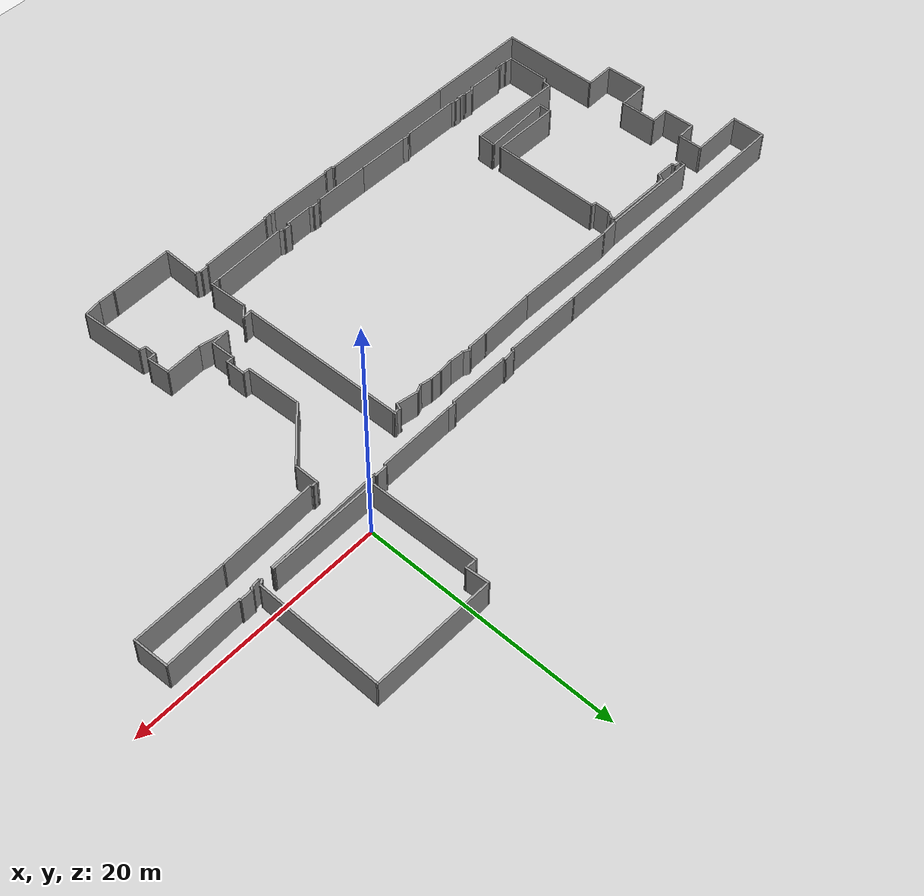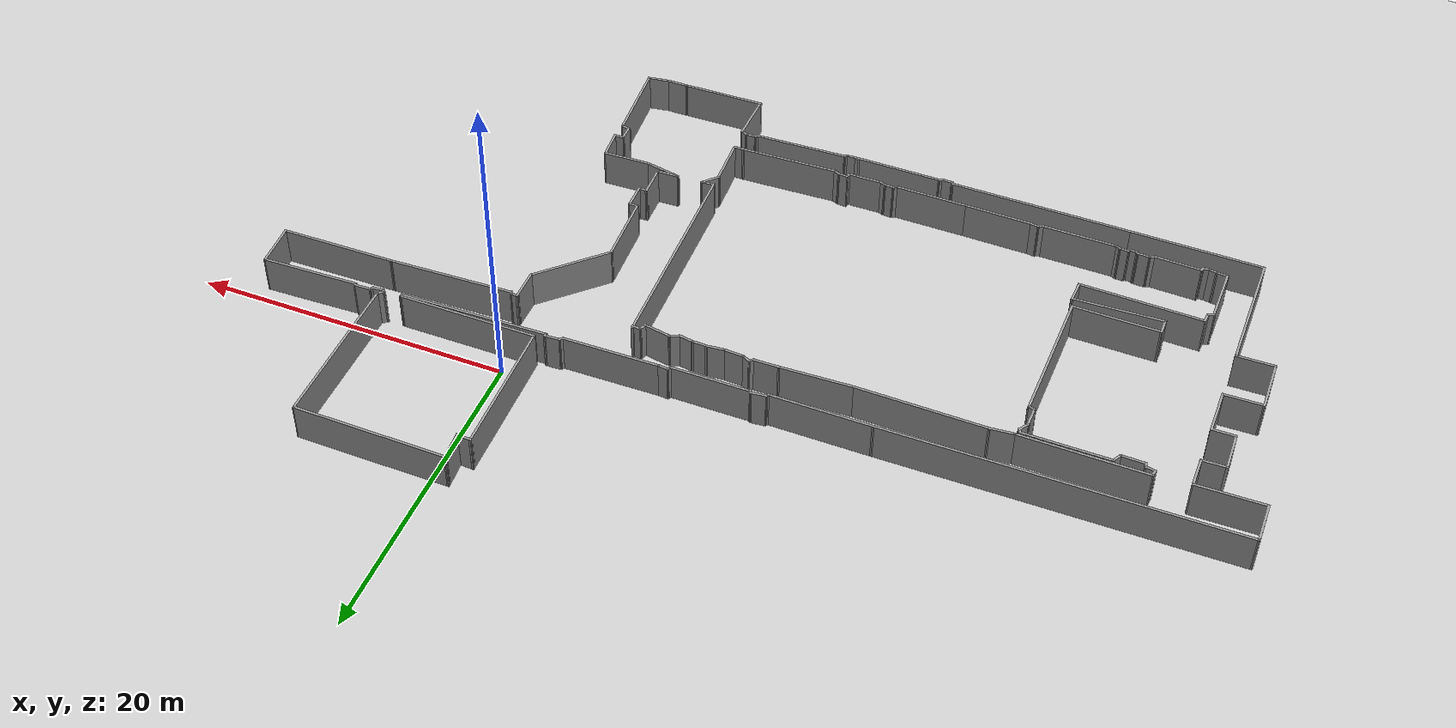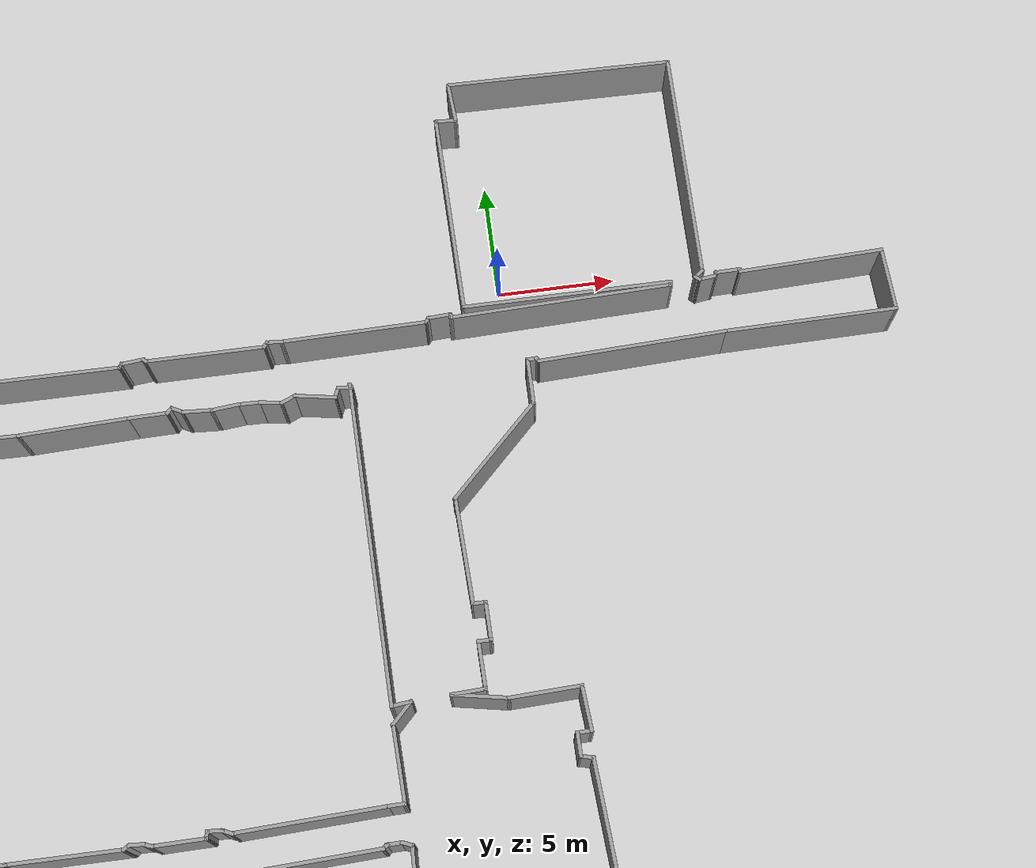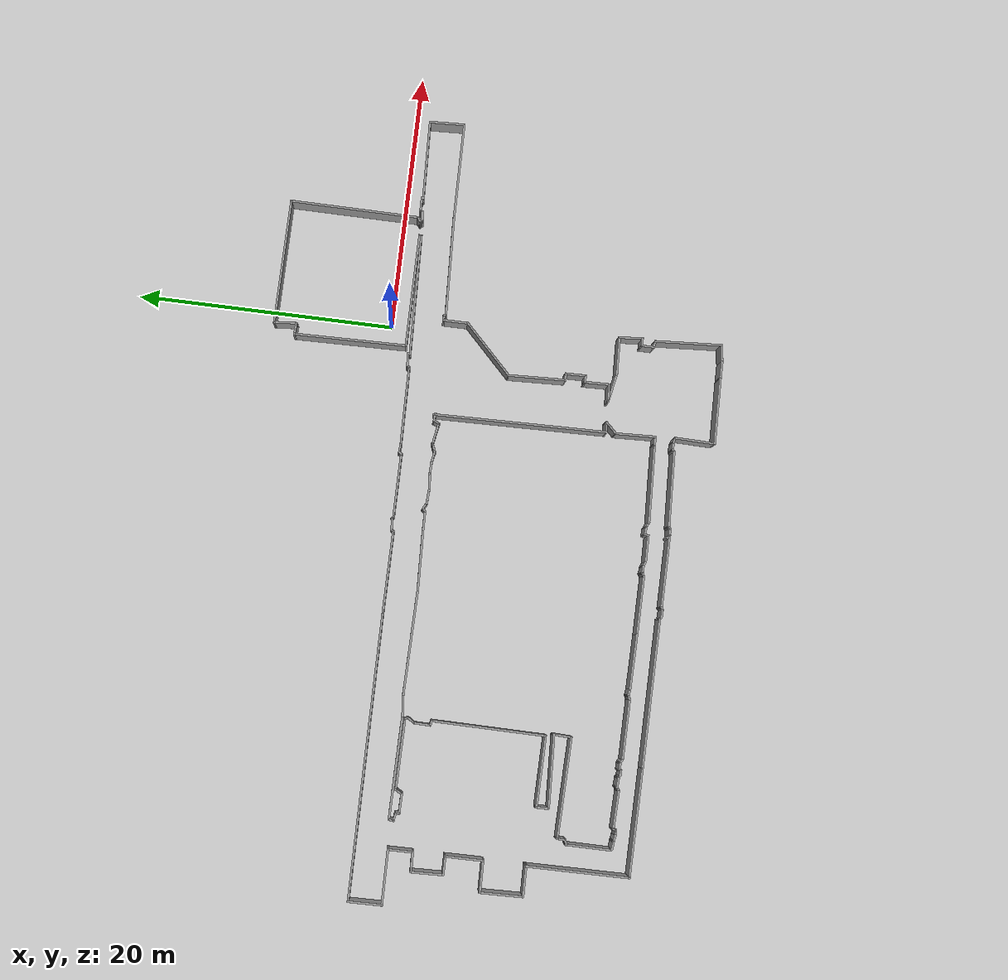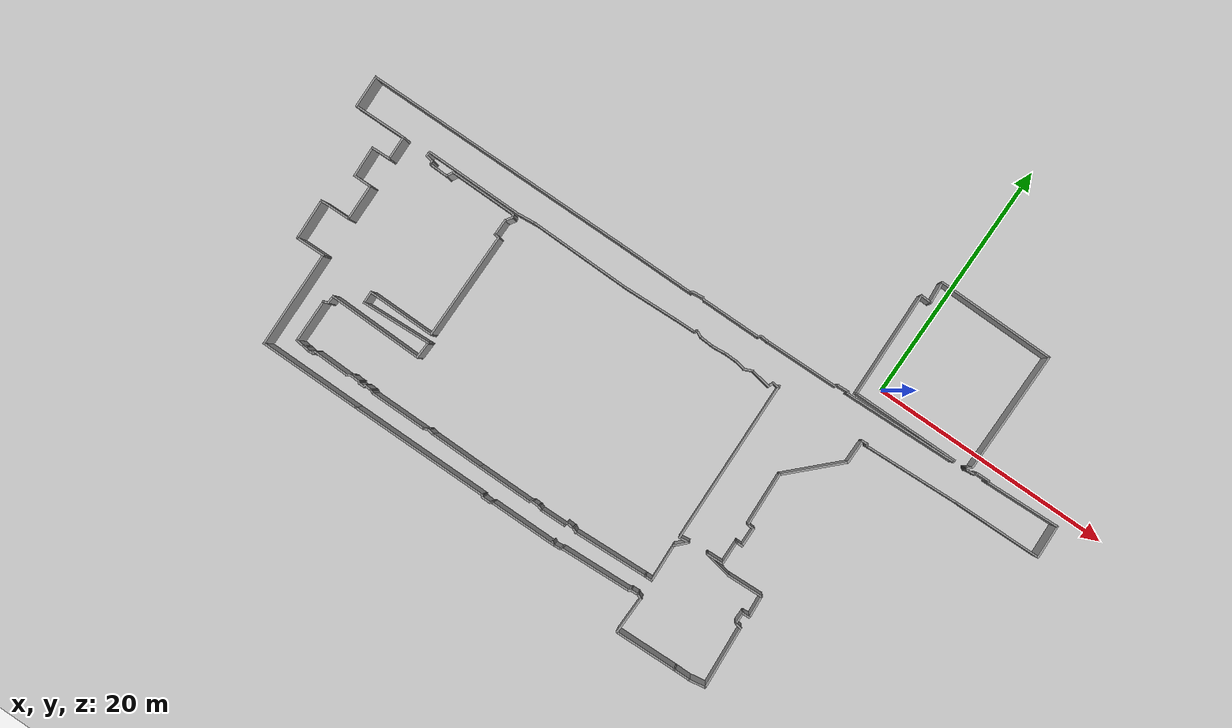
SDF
<sdf version="1.7">
 <world name="default">
  <light name="sun" type="directional">
   <pose>0 0 10 0 -0 0</pose>
   <diffuse>0.8 0.8 0.8 1</diffuse>
   <specular>0.2 0.2 0.2 1</specular>
   <attenuation>
    <range>1000</range>
    <constant>0.9</constant>
    <linear>0.01</linear>
    <quadratic>0.001</quadratic>
   </attenuation>
   <direction>-0.5 0.1 -0.9</direction>
   <spot><inner_angle>0</inner_angle><outer_angle>0</outer_angle><falloff>0</falloff></spot>
  </light>
  <model name="ground_plane">
   <static>1</static>
   <link name="link">
    <collision name="collision">
     <geometry><plane><normal>0 0 1</normal><size>100 100</size></plane></geometry>
     <surface>
      <contact><collide_bitmask>65535</collide_bitmask></contact>
      <friction><ode><mu>100</mu><mu2>50</mu2></ode></friction>
     </surface>
    </collision>
    <visual name="visual">
     <cast_shadows>0</cast_shadows>
     <geometry><plane><normal>0 0 1</normal><size>100 100</size></plane></geometry>
     <material>
      <script><uri>file://media/materials/scripts/gazebo.material</uri><name>Gazebo/Grey</name></script>
     </material>
    </visual>
   </link>
  </model>
  <gravity>0 0 -9.8</gravity>
  <magnetic_field>6e-06 2.3e-05 -4.2e-05</magnetic_field>
  <atmosphere type="adiabatic"/>
  <physics type="ode">
   <max_step_size>0.001</max_step_size>
   <real_time_factor>1</real_time_factor>
   <real_time_update_rate>1000</real_time_update_rate>
  </physics>
  <scene><ambient>0.4 0.4 0.4 1</ambient><background>0.7 0.7 0.7 1</background><shadows>1</shadows></scene>
  <spherical_coordinates>
   <surface_model>EARTH_WGS84</surface_model>
   <latitude_deg>0</latitude_deg>
   <longitude_deg>0</longitude_deg>
   <elevation>0</elevation>
   <heading_deg>0</heading_deg>
  </spherical_coordinates>
  <model name="EnvDC_1stfloor">
   <pose>-14.254 -7.77363 0 0 0 -0.048671</pose>
   <link name="Wall_0">
    <collision name="Wall_0_Collision">
     <geometry><box><size>1 0.15 2.5</size></box></geometry>
     <pose>0 0 1.25 0 -0 0</pose>
    </collision>
    <visual name="Wall_0_Visual">
     <pose>0 0 1.25 0 -0 0</pose>
     <geometry><box><size>1 0.15 2.5</size></box></geometry>
     <material>
      <script><uri>file://media/materials/scripts/gazebo.material</uri><name>Gazebo/Grey</name></script>
      <ambient>1 1 1 1</ambient>
     </material>
     <meta><layer>0</layer></meta>
    </visual>
    <pose>12.1528 15.725 0 0 -0 0</pose>
   </link>
   <link name="Wall_1">
    <collision name="Wall_1_Collision">
     <geometry><box><size>1.87529 0.15 2.5</size></box></geometry>
     <pose>0 0 1.25 0 -0 0</pose>
    </collision>
    <visual name="Wall_1_Visual">
     <pose>0 0 1.25 0 -0 0</pose>
     <geometry><box><size>1.87529 0.15 2.5</size></box></geometry>
     <material>
      <script><uri>file://media/materials/scripts/gazebo.material</uri><name>Gazebo/Grey</name></script>
      <ambient>1 1 1 1</ambient>
     </material>
     <meta><layer>0</layer></meta>
    </visual>
    <pose>12.4735 16.5813 0 0 -0 1.69199</pose>
   </link>
   <link name="Wall_10">
    <collision name="Wall_10_Collision">
     <geometry><box><size>0.255426 0.15 2.5</size></box></geometry>
     <pose>0 0 1.25 0 -0 0</pose>
    </collision>
    <visual name="Wall_10_Visual">
     <pose>0 0 1.25 0 -0 0</pose>
     <geometry><box><size>0.255426 0.15 2.5</size></box></geometry>
     <material>
      <script><uri>file://media/materials/scripts/gazebo.material</uri><name>Gazebo/Grey</name></script>
      <ambient>1 1 1 1</ambient>
     </material>
     <meta><layer>0</layer></meta>
    </visual>
    <pose>24.0145 7.75655 0 0 -0 -1.35213</pose>
   </link>
   <link name="Wall_100">
    <collision name="Wall_100_Collision">
     <geometry><box><size>0.755861 0.15 2.5</size></box></geometry>
     <pose>0 0 1.25 0 -0 0</pose>
    </collision>
    <visual name="Wall_100_Visual">
     <pose>0 0 1.25 0 -0 0</pose>
     <geometry><box><size>0.755861 0.15 2.5</size></box></geometry>
     <material>
      <script><uri>file://media/materials/scripts/gazebo.material</uri><name>Gazebo/Grey</name></script>
      <ambient>1 1 1 1</ambient>
     </material>
     <meta><layer>0</layer></meta>
    </visual>
    <pose>8.31616 -13.2267 0 0 -0 -3.07717</pose>
   </link>
   <link name="Wall_101">
    <collision name="Wall_101_Collision">
     <geometry><box><size>6.22065 0.15 2.5</size></box></geometry>
     <pose>0 0 1.25 0 -0 0</pose>
    </collision>
    <visual name="Wall_101_Visual">
     <pose>0 0 1.25 0 -0 0</pose>
     <geometry><box><size>6.22065 0.15 2.5</size></box></geometry>
     <material>
      <script><uri>file://media/materials/scripts/gazebo.material</uri><name>Gazebo/Grey</name></script>
      <ambient>1 1 1 1</ambient>
     </material>
     <meta><layer>0</layer></meta>
    </visual>
    <pose>4.99084 -13.5192 0 0 -0 -3.05152</pose>
   </link>
   <link name="Wall_102">
    <collision name="Wall_102_Collision">
     <geometry><box><size>0.544913 0.15 2.5</size></box></geometry>
     <pose>0 0 1.25 0 -0 0</pose>
    </collision>
    <visual name="Wall_102_Visual">
     <pose>0 0 1.25 0 -0 0</pose>
     <geometry><box><size>0.544913 0.15 2.5</size></box></geometry>
     <material>
      <script><uri>file://media/materials/scripts/gazebo.material</uri><name>Gazebo/Grey</name></script>
      <ambient>1 1 1 1</ambient>
     </material>
     <meta><layer>0</layer></meta>
    </visual>
    <pose>1.78254 -13.724 0 0 -0 2.7886</pose>
   </link>
   <link name="Wall_103">
    <collision name="Wall_103_Collision">
     <geometry><box><size>0.715933 0.15 2.5</size></box></geometry>
     <pose>0 0 1.25 0 -0 0</pose>
    </collision>
    <visual name="Wall_103_Visual">
     <pose>0 0 1.25 0 -0 0</pose>
     <geometry><box><size>0.715933 0.15 2.5</size></box></geometry>
     <material>
      <script><uri>file://media/materials/scripts/gazebo.material</uri><name>Gazebo/Grey</name></script>
      <ambient>1 1 1 1</ambient>
     </material>
     <meta><layer>0</layer></meta>
    </visual>
    <pose>1.31446 -13.646 0 0 -0 3.10712</pose>
   </link>
   <link name="Wall_104">
    <collision name="Wall_104_Collision">
     <geometry><box><size>0.420217 0.15 2.5</size></box></geometry>
     <pose>0 0 1.25 0 -0 0</pose>
    </collision>
    <visual name="Wall_104_Visual">
     <pose>0 0 1.25 0 -0 0</pose>
     <geometry><box><size>0.420217 0.15 2.5</size></box></geometry>
     <material>
      <script><uri>file://media/materials/scripts/gazebo.material</uri><name>Gazebo/Grey</name></script>
      <ambient>1 1 1 1</ambient>
     </material>
     <meta><layer>0</layer></meta>
    </visual>
    <pose>1.00864 -13.7694 0 0 -0 -1.74203</pose>
   </link>
   <link name="Wall_105">
    <collision name="Wall_105_Collision">
     <geometry><box><size>2.22808 0.15 2.5</size></box></geometry>
     <pose>0 0 1.25 0 -0 0</pose>
    </collision>
    <visual name="Wall_105_Visual">
     <pose>0 0 1.25 0 -0 0</pose>
     <geometry><box><size>2.22808 0.15 2.5</size></box></geometry>
     <material>
      <script><uri>file://media/materials/scripts/gazebo.material</uri><name>Gazebo/Grey</name></script>
      <ambient>1 1 1 1</ambient>
     </material>
     <meta><layer>0</layer></meta>
    </visual>
    <pose>-0.051496 -13.9658 0 0 -0 -3.08063</pose>
   </link>
   <link name="Wall_11">
    <collision name="Wall_11_Collision">
     <geometry><box><size>6.22574 0.15 2.5</size></box></geometry>
     <pose>0 0 1.25 0 -0 0</pose>
    </collision>
    <visual name="Wall_11_Visual">
     <pose>0 0 1.25 0 -0 0</pose>
     <geometry><box><size>6.22574 0.15 2.5</size></box></geometry>
     <material>
      <script><uri>file://media/materials/scripts/gazebo.material</uri><name>Gazebo/Grey</name></script>
      <ambient>1 1 1 1</ambient>
     </material>
     <meta><layer>0</layer></meta>
    </visual>
    <pose>27.0534 7.95666 0 0 -0 0.082907</pose>
   </link>
   <link name="Wall_111">
    <collision name="Wall_111_Collision">
     <geometry><box><size>0.496157 0.15 2.5</size></box></geometry>
     <pose>0 0 1.25 0 -0 0</pose>
    </collision>
    <visual name="Wall_111_Visual">
     <pose>0 0 1.25 0 -0 0</pose>
     <geometry><box><size>0.496157 0.15 2.5</size></box></geometry>
     <material>
      <script><uri>file://media/materials/scripts/gazebo.material</uri><name>Gazebo/Grey</name></script>
      <ambient>1 1 1 1</ambient>
     </material>
     <meta><layer>0</layer></meta>
    </visual>
    <pose>-1.25341 -13.9763 0 0 -0 2.8312</pose>
   </link>
   <link name="Wall_112">
    <collision name="Wall_112_Collision">
     <geometry><box><size>0.682216 0.15 2.5</size></box></geometry>
     <pose>0 0 1.25 0 -0 0</pose>
    </collision>
    <visual name="Wall_112_Visual">
     <pose>0 0 1.25 0 -0 0</pose>
     <geometry><box><size>0.682216 0.15 2.5</size></box></geometry>
     <material>
      <script><uri>file://media/materials/scripts/gazebo.material</uri><name>Gazebo/Grey</name></script>
      <ambient>1 1 1 1</ambient>
     </material>
     <meta><layer>0</layer></meta>
    </visual>
    <pose>-1.68433 -13.9234 0 0 -0 3.14159</pose>
   </link>
   <link name="Wall_113">
    <collision name="Wall_113_Collision">
     <geometry><box><size>0.403477 0.15 2.5</size></box></geometry>
     <pose>0 0 1.25 0 -0 0</pose>
    </collision>
    <visual name="Wall_113_Visual">
     <pose>0 0 1.25 0 -0 0</pose>
     <geometry><box><size>0.403477 0.15 2.5</size></box></geometry>
     <material>
      <script><uri>file://media/materials/scripts/gazebo.material</uri><name>Gazebo/Grey</name></script>
      <ambient>1 1 1 1</ambient>
     </material>
     <meta><layer>0</layer></meta>
    </visual>
    <pose>-2.05615 -13.9933 0 0 -0 -2.55732</pose>
   </link>
   <link name="Wall_114">
    <collision name="Wall_114_Collision">
     <geometry><box><size>4.64567 0.15 2.5</size></box></geometry>
     <pose>0 0 1.25 0 -0 0</pose>
    </collision>
    <visual name="Wall_114_Visual">
     <pose>0 0 1.25 0 -0 0</pose>
     <geometry><box><size>4.64567 0.15 2.5</size></box></geometry>
     <material>
      <script><uri>file://media/materials/scripts/gazebo.material</uri><name>Gazebo/Grey</name></script>
      <ambient>1 1 1 1</ambient>
     </material>
     <meta><layer>0</layer></meta>
    </visual>
    <pose>-4.40738 -14.1701 0 0 -0 -3.09617</pose>
   </link>
   <link name="Wall_116">
    <collision name="Wall_116_Collision">
     <geometry><box><size>4.34413 0.15 2.5</size></box></geometry>
     <pose>0 0 1.25 0 -0 0</pose>
    </collision>
    <visual name="Wall_116_Visual">
     <pose>0 0 1.25 0 -0 0</pose>
     <geometry><box><size>4.34413 0.15 2.5</size></box></geometry>
     <material>
      <script><uri>file://media/materials/scripts/gazebo.material</uri><name>Gazebo/Grey</name></script>
      <ambient>1 1 1 1</ambient>
     </material>
     <meta><layer>0</layer></meta>
    </visual>
    <pose>-8.74854 -14.3495 0 0 -0 -3.10472</pose>
   </link>
   <link name="Wall_117">
    <collision name="Wall_117_Collision">
     <geometry><box><size>0.657664 0.15 2.5</size></box></geometry>
     <pose>0 0 1.25 0 -0 0</pose>
    </collision>
    <visual name="Wall_117_Visual">
     <pose>0 0 1.25 0 -0 0</pose>
     <geometry><box><size>0.657664 0.15 2.5</size></box></geometry>
     <material>
      <script><uri>file://media/materials/scripts/gazebo.material</uri><name>Gazebo/Grey</name></script>
      <ambient>1 1 1 1</ambient>
     </material>
     <meta><layer>0</layer></meta>
    </visual>
    <pose>-11.0971 -14.4057 0 0 -0 3.05845</pose>
   </link>
   <link name="Wall_118">
    <collision name="Wall_118_Collision">
     <geometry><box><size>0.478084 0.15 2.5</size></box></geometry>
     <pose>0 0 1.25 0 -0 0</pose>
    </collision>
    <visual name="Wall_118_Visual">
     <pose>0 0 1.25 0 -0 0</pose>
     <geometry><box><size>0.478084 0.15 2.5</size></box></geometry>
     <material>
      <script><uri>file://media/materials/scripts/gazebo.material</uri><name>Gazebo/Grey</name></script>
      <ambient>1 1 1 1</ambient>
     </material>
     <meta><layer>0</layer></meta>
    </visual>
    <pose>-11.4976 -14.4563 0 0 -0 -2.68944</pose>
   </link>
   <link name="Wall_119">
    <collision name="Wall_119_Collision">
     <geometry><box><size>4.75823 0.15 2.5</size></box></geometry>
     <pose>0 0 1.25 0 -0 0</pose>
    </collision>
    <visual name="Wall_119_Visual">
     <pose>0 0 1.25 0 -0 0</pose>
     <geometry><box><size>4.75823 0.15 2.5</size></box></geometry>
     <material>
      <script><uri>file://media/materials/scripts/gazebo.material</uri><name>Gazebo/Grey</name></script>
      <ambient>1 1 1 1</ambient>
     </material>
     <meta><layer>0</layer></meta>
    </visual>
    <pose>-13.9471 -14.6292 0 0 -0 -3.09767</pose>
   </link>
   <link name="Wall_12">
    <collision name="Wall_12_Collision">
     <geometry><box><size>2.83708 0.15 2.5</size></box></geometry>
     <pose>0 0 1.25 0 -0 0</pose>
    </collision>
    <visual name="Wall_12_Visual">
     <pose>0 0 1.25 0 -0 0</pose>
     <geometry><box><size>2.83708 0.15 2.5</size></box></geometry>
     <material>
      <script><uri>file://media/materials/scripts/gazebo.material</uri><name>Gazebo/Grey</name></script>
      <ambient>1 1 1 1</ambient>
     </material>
     <meta><layer>0</layer></meta>
    </visual>
    <pose>30.2037 6.87033 0 0 -0 -1.47917</pose>
   </link>
   <link name="Wall_121">
    <collision name="Wall_121_Collision">
     <geometry><box><size>0.441234 0.15 2.5</size></box></geometry>
     <pose>0 0 1.25 0 -0 0</pose>
    </collision>
    <visual name="Wall_121_Visual">
     <pose>0 0 1.25 0 -0 0</pose>
     <geometry><box><size>0.441234 0.15 2.5</size></box></geometry>
     <material>
      <script><uri>file://media/materials/scripts/gazebo.material</uri><name>Gazebo/Grey</name></script>
      <ambient>1 1 1 1</ambient>
     </material>
     <meta><layer>0</layer></meta>
    </visual>
    <pose>-16.3839 -14.6755 0 0 -0 2.75571</pose>
   </link>
   <link name="Wall_122">
    <collision name="Wall_122_Collision">
     <geometry><box><size>0.664342 0.15 2.5</size></box></geometry>
     <pose>0 0 1.25 0 -0 0</pose>
    </collision>
    <visual name="Wall_122_Visual">
     <pose>0 0 1.25 0 -0 0</pose>
     <geometry><box><size>0.664342 0.15 2.5</size></box></geometry>
     <material>
      <script><uri>file://media/materials/scripts/gazebo.material</uri><name>Gazebo/Grey</name></script>
      <ambient>1 1 1 1</ambient>
     </material>
     <meta><layer>0</layer></meta>
    </visual>
    <pose>-16.776 -14.6207 0 0 -0 3.14159</pose>
   </link>
   <link name="Wall_123">
    <collision name="Wall_123_Collision">
     <geometry><box><size>0.272769 0.15 2.5</size></box></geometry>
     <pose>0 0 1.25 0 -0 0</pose>
    </collision>
    <visual name="Wall_123_Visual">
     <pose>0 0 1.25 0 -0 0</pose>
     <geometry><box><size>0.272769 0.15 2.5</size></box></geometry>
     <material>
      <script><uri>file://media/materials/scripts/gazebo.material</uri><name>Gazebo/Grey</name></script>
      <ambient>1 1 1 1</ambient>
     </material>
     <meta><layer>0</layer></meta>
    </visual>
    <pose>-17.05 -14.6798 0 0 -0 -1.8491</pose>
   </link>
   <link name="Wall_124">
    <collision name="Wall_124_Collision">
     <geometry><box><size>0.58878 0.15 2.5</size></box></geometry>
     <pose>0 0 1.25 0 -0 0</pose>
    </collision>
    <visual name="Wall_124_Visual">
     <pose>0 0 1.25 0 -0 0</pose>
     <geometry><box><size>0.58878 0.15 2.5</size></box></geometry>
     <material>
      <script><uri>file://media/materials/scripts/gazebo.material</uri><name>Gazebo/Grey</name></script>
      <ambient>1 1 1 1</ambient>
     </material>
     <meta><layer>0</layer></meta>
    </visual>
    <pose>-17.2861 -14.743 0 0 -0 -3.12236</pose>
   </link>
   <link name="Wall_125">
    <collision name="Wall_125_Collision">
     <geometry><box><size>0.309092 0.15 2.5</size></box></geometry>
     <pose>0 0 1.25 0 -0 0</pose>
    </collision>
    <visual name="Wall_125_Visual">
     <pose>0 0 1.25 0 -0 0</pose>
     <geometry><box><size>0.309092 0.15 2.5</size></box></geometry>
     <material>
      <script><uri>file://media/materials/scripts/gazebo.material</uri><name>Gazebo/Grey</name></script>
      <ambient>1 1 1 1</ambient>
     </material>
     <meta><layer>0</layer></meta>
    </visual>
    <pose>-17.5728 -14.7051 0 0 -0 2.58299</pose>
   </link>
   <link name="Wall_126">
    <collision name="Wall_126_Collision">
     <geometry><box><size>0.875138 0.15 2.5</size></box></geometry>
     <pose>0 0 1.25 0 -0 0</pose>
    </collision>
    <visual name="Wall_126_Visual">
     <pose>0 0 1.25 0 -0 0</pose>
     <geometry><box><size>0.875138 0.15 2.5</size></box></geometry>
     <material>
      <script><uri>file://media/materials/scripts/gazebo.material</uri><name>Gazebo/Grey</name></script>
      <ambient>1 1 1 1</ambient>
     </material>
     <meta><layer>0</layer></meta>
    </visual>
    <pose>-18.0028 -14.6629 0 0 -0 3.14159</pose>
   </link>
   <link name="Wall_127">
    <collision name="Wall_127_Collision">
     <geometry><box><size>0.449419 0.15 2.5</size></box></geometry>
     <pose>0 0 1.25 0 -0 0</pose>
    </collision>
    <visual name="Wall_127_Visual">
     <pose>0 0 1.25 0 -0 0</pose>
     <geometry><box><size>0.449419 0.15 2.5</size></box></geometry>
     <material>
      <script><uri>file://media/materials/scripts/gazebo.material</uri><name>Gazebo/Grey</name></script>
      <ambient>1 1 1 1</ambient>
     </material>
     <meta><layer>0</layer></meta>
    </visual>
    <pose>-18.4919 -14.743 0 0 -0 -2.57702</pose>
   </link>
   <link name="Wall_128">
    <collision name="Wall_128_Collision">
     <geometry><box><size>3.06046 0.15 2.5</size></box></geometry>
     <pose>0 0 1.25 0 -0 0</pose>
    </collision>
    <visual name="Wall_128_Visual">
     <pose>0 0 1.25 0 -0 0</pose>
     <geometry><box><size>3.06046 0.15 2.5</size></box></geometry>
     <material>
      <script><uri>file://media/materials/scripts/gazebo.material</uri><name>Gazebo/Grey</name></script>
      <ambient>1 1 1 1</ambient>
     </material>
     <meta><layer>0</layer></meta>
    </visual>
    <pose>-20.0728 -14.8568 0 0 -0 -3.11841</pose>
   </link>
   <link name="Wall_129">
    <collision name="Wall_129_Collision">
     <geometry><box><size>0.342276 0.15 2.5</size></box></geometry>
     <pose>0 0 1.25 0 -0 0</pose>
    </collision>
    <visual name="Wall_129_Visual">
     <pose>0 0 1.25 0 -0 0</pose>
     <geometry><box><size>0.342276 0.15 2.5</size></box></geometry>
     <material>
      <script><uri>file://media/materials/scripts/gazebo.material</uri><name>Gazebo/Grey</name></script>
      <ambient>1 1 1 1</ambient>
     </material>
     <meta><layer>0</layer></meta>
    </visual>
    <pose>-21.5526 -14.9833 0 0 -0 -1.83705</pose>
   </link>
   <link name="Wall_130">
    <collision name="Wall_130_Collision">
     <geometry><box><size>0.532791 0.15 2.5</size></box></geometry>
     <pose>0 0 1.25 0 -0 0</pose>
    </collision>
    <visual name="Wall_130_Visual">
     <pose>0 0 1.25 0 -0 0</pose>
     <geometry><box><size>0.532791 0.15 2.5</size></box></geometry>
     <material>
      <script><uri>file://media/materials/scripts/gazebo.material</uri><name>Gazebo/Grey</name></script>
      <ambient>1 1 1 1</ambient>
     </material>
     <meta><layer>0</layer></meta>
    </visual>
    <pose>-21.7676 -15.1014 0 0 -0 -3.00904</pose>
   </link>
   <link name="Wall_131">
    <collision name="Wall_131_Collision">
     <geometry><box><size>0.634225 0.15 2.5</size></box></geometry>
     <pose>0 0 1.25 0 -0 0</pose>
    </collision>
    <visual name="Wall_131_Visual">
     <pose>0 0 1.25 0 -0 0</pose>
     <geometry><box><size>0.634225 0.15 2.5</size></box></geometry>
     <material>
      <script><uri>file://media/materials/scripts/gazebo.material</uri><name>Gazebo/Grey</name></script>
      <ambient>1 1 1 1</ambient>
     </material>
     <meta><layer>0</layer></meta>
    </visual>
    <pose>-22.1977 -15.1014 0 0 -0 3.03672</pose>
   </link>
   <link name="Wall_132">
    <collision name="Wall_132_Collision">
     <geometry><box><size>0.817448 0.15 2.5</size></box></geometry>
     <pose>0 0 1.25 0 -0 0</pose>
    </collision>
    <visual name="Wall_132_Visual">
     <pose>0 0 1.25 0 -0 0</pose>
     <geometry><box><size>0.817448 0.15 2.5</size></box></geometry>
     <material>
      <script><uri>file://media/materials/scripts/gazebo.material</uri><name>Gazebo/Grey</name></script>
      <ambient>1 1 1 1</ambient>
     </material>
     <meta><layer>0</layer></meta>
    </visual>
    <pose>-22.771 -15.055 0 0 -0 3.07839</pose>
   </link>
   <link name="Wall_133">
    <collision name="Wall_133_Collision">
     <geometry><box><size>3.62843 0.15 2.5</size></box></geometry>
     <pose>0 0 1.25 0 -0 0</pose>
    </collision>
    <visual name="Wall_133_Visual">
     <pose>0 0 1.25 0 -0 0</pose>
     <geometry><box><size>3.62843 0.15 2.5</size></box></geometry>
     <material>
      <script><uri>file://media/materials/scripts/gazebo.material</uri><name>Gazebo/Grey</name></script>
      <ambient>1 1 1 1</ambient>
     </material>
     <meta><layer>0</layer></meta>
    </visual>
    <pose>-23.1926 -13.2969 0 0 -0 1.62172</pose>
   </link>
   <link name="Wall_138">
    <collision name="Wall_138_Collision">
     <geometry><box><size>0.501012 0.15 2.5</size></box></geometry>
     <pose>0 0 1.25 0 -0 0</pose>
    </collision>
    <visual name="Wall_138_Visual">
     <pose>0 0 1.25 0 -0 0</pose>
     <geometry><box><size>0.501012 0.15 2.5</size></box></geometry>
     <material>
      <script><uri>file://media/materials/scripts/gazebo.material</uri><name>Gazebo/Grey</name></script>
      <ambient>1 1 1 1</ambient>
     </material>
     <meta><layer>0</layer></meta>
    </visual>
    <pose>-23.1209 -11.4883 0 0 -0 0.420663</pose>
   </link>
   <link name="Wall_139">
    <collision name="Wall_139_Collision">
     <geometry><box><size>0.748898 0.15 2.5</size></box></geometry>
     <pose>0 0 1.25 0 -0 0</pose>
    </collision>
    <visual name="Wall_139_Visual">
     <pose>0 0 1.25 0 -0 0</pose>
     <geometry><box><size>0.748898 0.15 2.5</size></box></geometry>
     <material>
      <script><uri>file://media/materials/scripts/gazebo.material</uri><name>Gazebo/Grey</name></script>
      <ambient>1 1 1 1</ambient>
     </material>
     <meta><layer>0</layer></meta>
    </visual>
    <pose>-22.9523 -11.1173 0 0 -0 1.54263</pose>
   </link>
   <link name="Wall_14">
    <collision name="Wall_14_Collision">
     <geometry><box><size>7.39108 0.15 2.5</size></box></geometry>
     <pose>0 0 1.25 0 -0 0</pose>
    </collision>
    <visual name="Wall_14_Visual">
     <pose>0 0 1.25 0 -0 0</pose>
     <geometry><box><size>7.39108 0.15 2.5</size></box></geometry>
     <material>
      <script><uri>file://media/materials/scripts/gazebo.material</uri><name>Gazebo/Grey</name></script>
      <ambient>1 1 1 1</ambient>
     </material>
     <meta><layer>0</layer></meta>
    </visual>
    <pose>26.713 5.30981 0 0 -0 -3.08007</pose>
   </link>
   <link name="Wall_140">
    <collision name="Wall_140_Collision">
     <geometry><box><size>7.85115 0.15 2.5</size></box></geometry>
     <pose>0 0 1.25 0 -0 0</pose>
    </collision>
    <visual name="Wall_140_Visual">
     <pose>0 0 1.25 0 -0 0</pose>
     <geometry><box><size>7.85115 0.15 2.5</size></box></geometry>
     <material>
      <script><uri>file://media/materials/scripts/gazebo.material</uri><name>Gazebo/Grey</name></script>
      <ambient>1 1 1 1</ambient>
     </material>
     <meta><layer>0</layer></meta>
    </visual>
    <pose>-19.0947 -10.7126 0 0 -0 0.027375</pose>
   </link>
   <link name="Wall_141">
    <collision name="Wall_141_Collision">
     <geometry><box><size>1.49069 0.15 2.5</size></box></geometry>
     <pose>0 0 1.25 0 -0 0</pose>
    </collision>
    <visual name="Wall_141_Visual">
     <pose>0 0 1.25 0 -0 0</pose>
     <geometry><box><size>1.49069 0.15 2.5</size></box></geometry>
     <material>
      <script><uri>file://media/materials/scripts/gazebo.material</uri><name>Gazebo/Grey</name></script>
      <ambient>1 1 1 1</ambient>
     </material>
     <meta><layer>0</layer></meta>
    </visual>
    <pose>-15.2498 -9.93685 0 0 -0 1.57709</pose>
   </link>
   <link name="Wall_142">
    <collision name="Wall_142_Collision">
     <geometry><box><size>5.7647 0.15 2.5</size></box></geometry>
     <pose>0 0 1.25 0 -0 0</pose>
    </collision>
    <visual name="Wall_142_Visual">
     <pose>0 0 1.25 0 -0 0</pose>
     <geometry><box><size>5.7647 0.15 2.5</size></box></geometry>
     <material>
      <script><uri>file://media/materials/scripts/gazebo.material</uri><name>Gazebo/Grey</name></script>
      <ambient>1 1 1 1</ambient>
     </material>
     <meta><layer>0</layer></meta>
    </visual>
    <pose>-18.0492 -9.52791 0 0 -0 -3.04835</pose>
   </link>
   <link name="Wall_143">
    <collision name="Wall_143_Collision">
     <geometry><box><size>1.07995 0.15 2.5</size></box></geometry>
     <pose>0 0 1.25 0 -0 0</pose>
    </collision>
    <visual name="Wall_143_Visual">
     <pose>0 0 1.25 0 -0 0</pose>
     <geometry><box><size>1.07995 0.15 2.5</size></box></geometry>
     <material>
      <script><uri>file://media/materials/scripts/gazebo.material</uri><name>Gazebo/Grey</name></script>
      <ambient>1 1 1 1</ambient>
     </material>
     <meta><layer>0</layer></meta>
    </visual>
    <pose>-20.8739 -9.32554 0 0 -0 1.63435</pose>
   </link>
   <link name="Wall_144">
    <collision name="Wall_144_Collision">
     <geometry><box><size>5.5923 0.15 2.5</size></box></geometry>
     <pose>0 0 1.25 0 -0 0</pose>
    </collision>
    <visual name="Wall_144_Visual">
     <pose>0 0 1.25 0 -0 0</pose>
     <geometry><box><size>5.5923 0.15 2.5</size></box></geometry>
     <material>
      <script><uri>file://media/materials/scripts/gazebo.material</uri><name>Gazebo/Grey</name></script>
      <ambient>1 1 1 1</ambient>
     </material>
     <meta><layer>0</layer></meta>
    </visual>
    <pose>-18.1841 -8.76061 0 0 -0 0.037192</pose>
   </link>
   <link name="Wall_146">
    <collision name="Wall_146_Collision">
     <geometry><box><size>8.90349 0.15 2.5</size></box></geometry>
     <pose>0 0 1.25 0 -0 0</pose>
    </collision>
    <visual name="Wall_146_Visual">
     <pose>0 0 1.25 0 -0 0</pose>
     <geometry><box><size>8.90349 0.15 2.5</size></box></geometry>
     <material>
      <script><uri>file://media/materials/scripts/gazebo.material</uri><name>Gazebo/Grey</name></script>
      <ambient>1 1 1 1</ambient>
     </material>
     <meta><layer>0</layer></meta>
    </visual>
    <pose>-15.6523 -4.2867 0 0 -0 1.61364</pose>
   </link>
   <link name="Wall_147">
    <collision name="Wall_147_Collision">
     <geometry><box><size>0.505025 0.15 2.5</size></box></geometry>
     <pose>0 0 1.25 0 -0 0</pose>
    </collision>
    <visual name="Wall_147_Visual">
     <pose>0 0 1.25 0 -0 0</pose>
     <geometry><box><size>0.505025 0.15 2.5</size></box></geometry>
     <material>
      <script><uri>file://media/materials/scripts/gazebo.material</uri><name>Gazebo/Grey</name></script>
      <ambient>1 1 1 1</ambient>
     </material>
     <meta><layer>0</layer></meta>
    </visual>
    <pose>-16.015 0.114301 0 0 -0 2.98168</pose>
   </link>
   <link name="Wall_148">
    <collision name="Wall_148_Collision">
     <geometry><box><size>1.40581 0.15 2.5</size></box></geometry>
     <pose>0 0 1.25 0 -0 0</pose>
    </collision>
    <visual name="Wall_148_Visual">
     <pose>0 0 1.25 0 -0 0</pose>
     <geometry><box><size>1.40581 0.15 2.5</size></box></geometry>
     <material>
      <script><uri>file://media/materials/scripts/gazebo.material</uri><name>Gazebo/Grey</name></script>
      <ambient>1 1 1 1</ambient>
     </material>
     <meta><layer>0</layer></meta>
    </visual>
    <pose>-16.2128 0.770066 0 0 -0 1.60682</pose>
   </link>
   <link name="Wall_149">
    <collision name="Wall_149_Collision">
     <geometry><box><size>0.753061 0.15 2.5</size></box></geometry>
     <pose>0 0 1.25 0 -0 0</pose>
    </collision>
    <visual name="Wall_149_Visual">
     <pose>0 0 1.25 0 -0 0</pose>
     <geometry><box><size>0.753061 0.15 2.5</size></box></geometry>
     <material>
      <script><uri>file://media/materials/scripts/gazebo.material</uri><name>Gazebo/Grey</name></script>
      <ambient>1 1 1 1</ambient>
     </material>
     <meta><layer>0</layer></meta>
    </visual>
    <pose>-16.0828 1.65761 0 0 -0 1.04002</pose>
   </link>
   <link name="Wall_150">
    <collision name="Wall_150_Collision">
     <geometry><box><size>0.402816 0.15 2.5</size></box></geometry>
     <pose>0 0 1.25 0 -0 0</pose>
    </collision>
    <visual name="Wall_150_Visual">
     <pose>0 0 1.25 0 -0 0</pose>
     <geometry><box><size>0.402816 0.15 2.5</size></box></geometry>
     <material>
      <script><uri>file://media/materials/scripts/gazebo.material</uri><name>Gazebo/Grey</name></script>
      <ambient>1 1 1 1</ambient>
     </material>
     <meta><layer>0</layer></meta>
    </visual>
    <pose>-15.9867 2.03072 0 0 -0 2.03444</pose>
   </link>
   <link name="Wall_151">
    <collision name="Wall_151_Collision">
     <geometry><box><size>5.54784 0.15 2.5</size></box></geometry>
     <pose>0 0 1.25 0 -0 0</pose>
    </collision>
    <visual name="Wall_151_Visual">
     <pose>0 0 1.25 0 -0 0</pose>
     <geometry><box><size>5.54784 0.15 2.5</size></box></geometry>
     <material>
      <script><uri>file://media/materials/scripts/gazebo.material</uri><name>Gazebo/Grey</name></script>
      <ambient>1 1 1 1</ambient>
     </material>
     <meta><layer>0</layer></meta>
    </visual>
    <pose>-18.7398 2.03072 0 0 -0 -3.09969</pose>
   </link>
   <link name="Wall_152">
    <collision name="Wall_152_Collision">
     <geometry><box><size>0.731478 0.15 2.5</size></box></geometry>
     <pose>0 0 1.25 0 -0 0</pose>
    </collision>
    <visual name="Wall_152_Visual">
     <pose>0 0 1.25 0 -0 0</pose>
     <geometry><box><size>0.731478 0.15 2.5</size></box></geometry>
     <material>
      <script><uri>file://media/materials/scripts/gazebo.material</uri><name>Gazebo/Grey</name></script>
      <ambient>1 1 1 1</ambient>
     </material>
     <meta><layer>0</layer></meta>
    </visual>
    <pose>-21.5664 1.65761 0 0 -0 -2.03444</pose>
   </link>
   <link name="Wall_153">
    <collision name="Wall_153_Collision">
     <geometry><box><size>1.60869 0.15 2.5</size></box></geometry>
     <pose>0 0 1.25 0 -0 0</pose>
    </collision>
    <visual name="Wall_153_Visual">
     <pose>0 0 1.25 0 -0 0</pose>
     <geometry><box><size>1.60869 0.15 2.5</size></box></geometry>
     <material>
      <script><uri>file://media/materials/scripts/gazebo.material</uri><name>Gazebo/Grey</name></script>
      <ambient>1 1 1 1</ambient>
     </material>
     <meta><layer>0</layer></meta>
    </visual>
    <pose>-22.4256 1.38061 0 0 -0 -3.11834</pose>
   </link>
   <link name="Wall_154">
    <collision name="Wall_154_Collision">
     <geometry><box><size>0.411026 0.15 2.5</size></box></geometry>
     <pose>0 0 1.25 0 -0 0</pose>
    </collision>
    <visual name="Wall_154_Visual">
     <pose>0 0 1.25 0 -0 0</pose>
     <geometry><box><size>0.411026 0.15 2.5</size></box></geometry>
     <material>
      <script><uri>file://media/materials/scripts/gazebo.material</uri><name>Gazebo/Grey</name></script>
      <ambient>1 1 1 1</ambient>
     </material>
     <meta><layer>0</layer></meta>
    </visual>
    <pose>-23.1945 1.48802 0 0 -0 1.87885</pose>
   </link>
   <link name="Wall_155">
    <collision name="Wall_155_Collision">
     <geometry><box><size>0.696925 0.15 2.5</size></box></geometry>
     <pose>0 0 1.25 0 -0 0</pose>
    </collision>
    <visual name="Wall_155_Visual">
     <pose>0 0 1.25 0 -0 0</pose>
     <geometry><box><size>0.696925 0.15 2.5</size></box></geometry>
     <material>
      <script><uri>file://media/materials/scripts/gazebo.material</uri><name>Gazebo/Grey</name></script>
      <ambient>1 1 1 1</ambient>
     </material>
     <meta><layer>0</layer></meta>
    </visual>
    <pose>-23.5054 1.6463 0 0 -0 3.01724</pose>
   </link>
   <link name="Wall_156">
    <collision name="Wall_156_Collision">
     <geometry><box><size>0.512507 0.15 2.5</size></box></geometry>
     <pose>0 0 1.25 0 -0 0</pose>
    </collision>
    <visual name="Wall_156_Visual">
     <pose>0 0 1.25 0 -0 0</pose>
     <geometry><box><size>0.512507 0.15 2.5</size></box></geometry>
     <material>
      <script><uri>file://media/materials/scripts/gazebo.material</uri><name>Gazebo/Grey</name></script>
      <ambient>1 1 1 1</ambient>
     </material>
     <meta><layer>0</layer></meta>
    </visual>
    <pose>-23.7654 1.86112 0 0 -0 1.50838</pose>
   </link>
   <link name="Wall_157">
    <collision name="Wall_157_Collision">
     <geometry><box><size>8.07119 0.15 2.5</size></box></geometry>
     <pose>0 0 1.25 0 -0 0</pose>
    </collision>
    <visual name="Wall_157_Visual">
     <pose>0 0 1.25 0 -0 0</pose>
     <geometry><box><size>8.07119 0.15 2.5</size></box></geometry>
     <material>
      <script><uri>file://media/materials/scripts/gazebo.material</uri><name>Gazebo/Grey</name></script>
      <ambient>1 1 1 1</ambient>
     </material>
     <meta><layer>0</layer></meta>
    </visual>
    <pose>-19.7969 2.20596 0 0 -0 0.041405</pose>
   </link>
   <link name="Wall_158">
    <collision name="Wall_158_Collision">
     <geometry><box><size>1.64662 0.15 2.5</size></box></geometry>
     <pose>0 0 1.25 0 -0 0</pose>
    </collision>
    <visual name="Wall_158_Visual">
     <pose>0 0 1.25 0 -0 0</pose>
     <geometry><box><size>1.64662 0.15 2.5</size></box></geometry>
     <material>
      <script><uri>file://media/materials/scripts/gazebo.material</uri><name>Gazebo/Grey</name></script>
      <ambient>1 1 1 1</ambient>
     </material>
     <meta><layer>0</layer></meta>
    </visual>
    <pose>-15.0992 2.47732 0 0 -0 0.144034</pose>
   </link>
   <link name="Wall_159">
    <collision name="Wall_159_Collision">
     <geometry><box><size>8.29544 0.15 2.5</size></box></geometry>
     <pose>0 0 1.25 0 -0 0</pose>
    </collision>
    <visual name="Wall_159_Visual">
     <pose>0 0 1.25 0 -0 0</pose>
     <geometry><box><size>8.29544 0.15 2.5</size></box></geometry>
     <material>
      <script><uri>file://media/materials/scripts/gazebo.material</uri><name>Gazebo/Grey</name></script>
      <ambient>1 1 1 1</ambient>
     </material>
     <meta><layer>0</layer></meta>
    </visual>
    <pose>-10.2883 2.72606 0 0 -0 0.034708</pose>
   </link>
   <link name="Wall_16">
    <collision name="Wall_16_Collision">
     <geometry><box><size>8.02507 0.15 2.5</size></box></geometry>
     <pose>0 0 1.25 0 -0 0</pose>
    </collision>
    <visual name="Wall_16_Visual">
     <pose>0 0 1.25 0 -0 0</pose>
     <geometry><box><size>8.02507 0.15 2.5</size></box></geometry>
     <material>
      <script><uri>file://media/materials/scripts/gazebo.material</uri><name>Gazebo/Grey</name></script>
      <ambient>1 1 1 1</ambient>
     </material>
     <meta><layer>0</layer></meta>
    </visual>
    <pose>19.1772 4.73871 0 0 -0 -3.05297</pose>
   </link>
   <link name="Wall_160">
    <collision name="Wall_160_Collision">
     <geometry><box><size>4.67756 0.15 2.5</size></box></geometry>
     <pose>0 0 1.25 0 -0 0</pose>
    </collision>
    <visual name="Wall_160_Visual">
     <pose>0 0 1.25 0 -0 0</pose>
     <geometry><box><size>4.67756 0.15 2.5</size></box></geometry>
     <material>
      <script><uri>file://media/materials/scripts/gazebo.material</uri><name>Gazebo/Grey</name></script>
      <ambient>1 1 1 1</ambient>
     </material>
     <meta><layer>0</layer></meta>
    </visual>
    <pose>-3.96247 3.05959 0 0 -0 0.085008</pose>
   </link>
   <link name="Wall_161">
    <collision name="Wall_161_Collision">
     <geometry><box><size>1.72564 0.15 2.5</size></box></geometry>
     <pose>0 0 1.25 0 -0 0</pose>
    </collision>
    <visual name="Wall_161_Visual">
     <pose>0 0 1.25 0 -0 0</pose>
     <geometry><box><size>1.72564 0.15 2.5</size></box></geometry>
     <material>
      <script><uri>file://media/materials/scripts/gazebo.material</uri><name>Gazebo/Grey</name></script>
      <ambient>1 1 1 1</ambient>
     </material>
     <meta><layer>0</layer></meta>
    </visual>
    <pose>-0.921076 3.30268 0 0 -0 0.064658</pose>
   </link>
   <link name="Wall_162">
    <collision name="Wall_162_Collision">
     <geometry><box><size>0.413948 0.15 2.5</size></box></geometry>
     <pose>0 0 1.25 0 -0 0</pose>
    </collision>
    <visual name="Wall_162_Visual">
     <pose>0 0 1.25 0 -0 0</pose>
     <geometry><box><size>0.413948 0.15 2.5</size></box></geometry>
     <material>
      <script><uri>file://media/materials/scripts/gazebo.material</uri><name>Gazebo/Grey</name></script>
      <ambient>1 1 1 1</ambient>
     </material>
     <meta><layer>0</layer></meta>
    </visual>
    <pose>-0.044838 3.44966 0 0 -0 0.815692</pose>
   </link>
   <link name="Wall_163">
    <collision name="Wall_163_Collision">
     <geometry><box><size>0.666637 0.15 2.5</size></box></geometry>
     <pose>0 0 1.25 0 -0 0</pose>
    </collision>
    <visual name="Wall_163_Visual">
     <pose>0 0 1.25 0 -0 0</pose>
     <geometry><box><size>0.666637 0.15 2.5</size></box></geometry>
     <material>
      <script><uri>file://media/materials/scripts/gazebo.material</uri><name>Gazebo/Grey</name></script>
      <ambient>1 1 1 1</ambient>
     </material>
     <meta><layer>0</layer></meta>
    </visual>
    <pose>0.283044 3.444 0 0 -0 -0.404892</pose>
   </link>
   <link name="Wall_164">
    <collision name="Wall_164_Collision">
     <geometry><box><size>1.32591 0.15 2.5</size></box></geometry>
     <pose>0 0 1.25 0 -0 0</pose>
    </collision>
    <visual name="Wall_164_Visual">
     <pose>0 0 1.25 0 -0 0</pose>
     <geometry><box><size>1.32591 0.15 2.5</size></box></geometry>
     <material>
      <script><uri>file://media/materials/scripts/gazebo.material</uri><name>Gazebo/Grey</name></script>
      <ambient>1 1 1 1</ambient>
     </material>
     <meta><layer>0</layer></meta>
    </visual>
    <pose>1.1084 3.33659 0 0 -0 -0.009615</pose>
   </link>
   <link name="Wall_165">
    <collision name="Wall_165_Collision">
     <geometry><box><size>1.25807 0.15 2.5</size></box></geometry>
     <pose>0 0 1.25 0 -0 0</pose>
    </collision>
    <visual name="Wall_165_Visual">
     <pose>0 0 1.25 0 -0 0</pose>
     <geometry><box><size>1.25807 0.15 2.5</size></box></geometry>
     <material>
      <script><uri>file://media/materials/scripts/gazebo.material</uri><name>Gazebo/Grey</name></script>
      <ambient>1 1 1 1</ambient>
     </material>
     <meta><layer>0</layer></meta>
    </visual>
    <pose>2.24469 3.41009 0 0 -0 0.14334</pose>
   </link>
   <link name="Wall_166">
    <collision name="Wall_166_Collision">
     <geometry><box><size>1.04384 0.15 2.5</size></box></geometry>
     <pose>0 0 1.25 0 -0 0</pose>
    </collision>
    <visual name="Wall_166_Visual">
     <pose>0 0 1.25 0 -0 0</pose>
     <geometry><box><size>1.04384 0.15 2.5</size></box></geometry>
     <material>
      <script><uri>file://media/materials/scripts/gazebo.material</uri><name>Gazebo/Grey</name></script>
      <ambient>1 1 1 1</ambient>
     </material>
     <meta><layer>0</layer></meta>
    </visual>
    <pose>3.23964 3.50054 0 0 -0 0.025311</pose>
   </link>
   <link name="Wall_167">
    <collision name="Wall_167_Collision">
     <geometry><box><size>1.02651 0.15 2.5</size></box></geometry>
     <pose>0 0 1.25 0 -0 0</pose>
    </collision>
    <visual name="Wall_167_Visual">
     <pose>0 0 1.25 0 -0 0</pose>
     <geometry><box><size>1.02651 0.15 2.5</size></box></geometry>
     <material>
      <script><uri>file://media/materials/scripts/gazebo.material</uri><name>Gazebo/Grey</name></script>
      <ambient>1 1 1 1</ambient>
     </material>
     <meta><layer>0</layer></meta>
    </visual>
    <pose>4.12153 3.46096 0 0 -0 -0.116355</pose>
   </link>
   <link name="Wall_168">
    <collision name="Wall_168_Collision">
     <geometry><box><size>0.777066 0.15 2.5</size></box></geometry>
     <pose>0 0 1.25 0 -0 0</pose>
    </collision>
    <visual name="Wall_168_Visual">
     <pose>0 0 1.25 0 -0 0</pose>
     <geometry><box><size>0.777066 0.15 2.5</size></box></geometry>
     <material>
      <script><uri>file://media/materials/scripts/gazebo.material</uri><name>Gazebo/Grey</name></script>
      <ambient>1 1 1 1</ambient>
     </material>
     <meta><layer>0</layer></meta>
    </visual>
    <pose>4.83948 3.54576 0 0 -0 0.44752</pose>
   </link>
   <link name="Wall_169">
    <collision name="Wall_169_Collision">
     <geometry><box><size>1.802 0.15 2.5</size></box></geometry>
     <pose>0 0 1.25 0 -0 0</pose>
    </collision>
    <visual name="Wall_169_Visual">
     <pose>0 0 1.25 0 -0 0</pose>
     <geometry><box><size>1.802 0.15 2.5</size></box></geometry>
     <material>
      <script><uri>file://media/materials/scripts/gazebo.material</uri><name>Gazebo/Grey</name></script>
      <ambient>1 1 1 1</ambient>
     </material>
     <meta><layer>0</layer></meta>
    </visual>
    <pose>5.94184 3.57968 0 0 -0 -0.123506</pose>
   </link>
   <link name="Wall_17">
    <collision name="Wall_17_Collision">
     <geometry><box><size>0.304061 0.15 2.5</size></box></geometry>
     <pose>0 0 1.25 0 -0 0</pose>
    </collision>
    <visual name="Wall_17_Visual">
     <pose>0 0 1.25 0 -0 0</pose>
     <geometry><box><size>0.304061 0.15 2.5</size></box></geometry>
     <material>
      <script><uri>file://media/materials/scripts/gazebo.material</uri><name>Gazebo/Grey</name></script>
      <ambient>1 1 1 1</ambient>
     </material>
     <meta><layer>0</layer></meta>
    </visual>
    <pose>15.2058 4.4494 0 0 -0 2.26553</pose>
   </link>
   <link name="Wall_170">
    <collision name="Wall_170_Collision">
     <geometry><box><size>0.582752 0.15 2.5</size></box></geometry>
     <pose>0 0 1.25 0 -0 0</pose>
    </collision>
    <visual name="Wall_170_Visual">
     <pose>0 0 1.25 0 -0 0</pose>
     <geometry><box><size>0.582752 0.15 2.5</size></box></geometry>
     <material>
      <script><uri>file://media/materials/scripts/gazebo.material</uri><name>Gazebo/Grey</name></script>
      <ambient>1 1 1 1</ambient>
     </material>
     <meta><layer>0</layer></meta>
    </visual>
    <pose>6.83504 3.68144 0 0 -0 1.22426</pose>
   </link>
   <link name="Wall_171">
    <collision name="Wall_171_Collision">
     <geometry><box><size>0.681877 0.15 2.5</size></box></geometry>
     <pose>0 0 1.25 0 -0 0</pose>
    </collision>
    <visual name="Wall_171_Visual">
     <pose>0 0 1.25 0 -0 0</pose>
     <geometry><box><size>0.681877 0.15 2.5</size></box></geometry>
     <material>
      <script><uri>file://media/materials/scripts/gazebo.material</uri><name>Gazebo/Grey</name></script>
      <ambient>1 1 1 1</ambient>
     </material>
     <meta><layer>0</layer></meta>
    </visual>
    <pose>7.17423 3.87364 0 0 -0 -0.042528</pose>
   </link>
   <link name="Wall_18">
    <collision name="Wall_18_Collision">
     <geometry><box><size>0.518444 0.15 2.5</size></box></geometry>
     <pose>0 0 1.25 0 -0 0</pose>
    </collision>
    <visual name="Wall_18_Visual">
     <pose>0 0 1.25 0 -0 0</pose>
     <geometry><box><size>0.518444 0.15 2.5</size></box></geometry>
     <material>
      <script><uri>file://media/materials/scripts/gazebo.material</uri><name>Gazebo/Grey</name></script>
      <ambient>1 1 1 1</ambient>
     </material>
     <meta><layer>0</layer></meta>
    </visual>
    <pose>14.9724 4.502 0 0 -0 -3.10589</pose>
   </link>
   <link name="Wall_19">
    <collision name="Wall_19_Collision">
     <geometry><box><size>2.05935 0.15 2.5</size></box></geometry>
     <pose>0 0 1.25 0 -0 0</pose>
    </collision>
    <visual name="Wall_19_Visual">
     <pose>0 0 1.25 0 -0 0</pose>
     <geometry><box><size>2.05935 0.15 2.5</size></box></geometry>
     <material>
      <script><uri>file://media/materials/scripts/gazebo.material</uri><name>Gazebo/Grey</name></script>
      <ambient>1 1 1 1</ambient>
     </material>
     <meta><layer>0</layer></meta>
    </visual>
    <pose>14.831 3.54203 0 0 -0 -1.526</pose>
   </link>
   <link name="Wall_2">
    <collision name="Wall_2_Collision">
     <geometry><box><size>9.80526 0.15 2.5</size></box></geometry>
     <pose>0 0 1.25 0 -0 0</pose>
    </collision>
    <visual name="Wall_2_Visual">
     <pose>0 0 1.25 0 -0 0</pose>
     <geometry><box><size>9.80526 0.15 2.5</size></box></geometry>
     <material>
      <script><uri>file://media/materials/scripts/gazebo.material</uri><name>Gazebo/Grey</name></script>
      <ambient>1 1 1 1</ambient>
     </material>
     <meta><layer>0</layer></meta>
    </visual>
    <pose>17.193 17.6228 0 0 -0 0.038364</pose>
   </link>
   <link name="Wall_21">
    <collision name="Wall_21_Collision">
     <geometry><box><size>5.30741 0.15 2.5</size></box></geometry>
     <pose>0 0 1.25 0 -0 0</pose>
    </collision>
    <visual name="Wall_21_Visual">
     <pose>0 0 1.25 0 -0 0</pose>
     <geometry><box><size>5.30741 0.15 2.5</size></box></geometry>
     <material>
      <script><uri>file://media/materials/scripts/gazebo.material</uri><name>Gazebo/Grey</name></script>
      <ambient>1 1 1 1</ambient>
     </material>
     <meta><layer>0</layer></meta>
    </visual>
    <pose>13.1327 0.686426 0 0 -0 -2.312</pose>
   </link>
   <link name="Wall_23">
    <collision name="Wall_23_Collision">
     <geometry><box><size>4.54645 0.15 2.5</size></box></geometry>
     <pose>0 0 1.25 0 -0 0</pose>
    </collision>
    <visual name="Wall_23_Visual">
     <pose>0 0 1.25 0 -0 0</pose>
     <geometry><box><size>4.54645 0.15 2.5</size></box></geometry>
     <material>
      <script><uri>file://media/materials/scripts/gazebo.material</uri><name>Gazebo/Grey</name></script>
      <ambient>1 1 1 1</ambient>
     </material>
     <meta><layer>0</layer></meta>
    </visual>
    <pose>11.5866 -3.40578 0 0 -0 -1.48199</pose>
   </link>
   <link name="Wall_24">
    <collision name="Wall_24_Collision">
     <geometry><box><size>0.66 0.15 2.5</size></box></geometry>
     <pose>0 0 1.25 0 -0 0</pose>
    </collision>
    <visual name="Wall_24_Visual">
     <pose>0 0 1.25 0 -0 0</pose>
     <geometry><box><size>0.66 0.15 2.5</size></box></geometry>
     <material>
      <script><uri>file://media/materials/scripts/gazebo.material</uri><name>Gazebo/Grey</name></script>
      <ambient>1 1 1 1</ambient>
     </material>
     <meta><layer>0</layer></meta>
    </visual>
    <pose>12.0366 -5.59578 0 0 -0 0</pose>
   </link>
   <link name="Wall_25">
    <collision name="Wall_25_Collision">
     <geometry><box><size>1.67329 0.15 2.5</size></box></geometry>
     <pose>0 0 1.25 0 -0 0</pose>
    </collision>
    <visual name="Wall_25_Visual">
     <pose>0 0 1.25 0 -0 0</pose>
     <geometry><box><size>1.67329 0.15 2.5</size></box></geometry>
     <material>
      <script><uri>file://media/materials/scripts/gazebo.material</uri><name>Gazebo/Grey</name></script>
      <ambient>1 1 1 1</ambient>
     </material>
     <meta><layer>0</layer></meta>
    </visual>
    <pose>12.3416 -6.35578 0 0 -0 -1.5051</pose>
   </link>
   <link name="Wall_26">
    <collision name="Wall_26_Collision">
     <geometry><box><size>0.6504 0.15 2.5</size></box></geometry>
     <pose>0 0 1.25 0 -0 0</pose>
    </collision>
    <visual name="Wall_26_Visual">
     <pose>0 0 1.25 0 -0 0</pose>
     <geometry><box><size>0.6504 0.15 2.5</size></box></geometry>
     <material>
      <script><uri>file://media/materials/scripts/gazebo.material</uri><name>Gazebo/Grey</name></script>
      <ambient>1 1 1 1</ambient>
     </material>
     <meta><layer>0</layer></meta>
    </visual>
    <pose>12.1416 -7.12578 0 0 -0 -3.10161</pose>
   </link>
   <link name="Wall_27">
    <collision name="Wall_27_Collision">
     <geometry><box><size>2.05444 0.15 2.5</size></box></geometry>
     <pose>0 0 1.25 0 -0 0</pose>
    </collision>
    <visual name="Wall_27_Visual">
     <pose>0 0 1.25 0 -0 0</pose>
     <geometry><box><size>2.05444 0.15 2.5</size></box></geometry>
     <material>
      <script><uri>file://media/materials/scripts/gazebo.material</uri><name>Gazebo/Grey</name></script>
      <ambient>1 1 1 1</ambient>
     </material>
     <meta><layer>0</layer></meta>
    </visual>
    <pose>11.9616 -8.08578 0 0 -0 -1.49724</pose>
   </link>
   <link name="Wall_28">
    <collision name="Wall_28_Collision">
     <geometry><box><size>1.4854 0.15 2.5</size></box></geometry>
     <pose>0 0 1.25 0 -0 0</pose>
    </collision>
    <visual name="Wall_28_Visual">
     <pose>0 0 1.25 0 -0 0</pose>
     <geometry><box><size>1.4854 0.15 2.5</size></box></geometry>
     <material>
      <script><uri>file://media/materials/scripts/gazebo.material</uri><name>Gazebo/Grey</name></script>
      <ambient>1 1 1 1</ambient>
     </material>
     <meta><layer>0</layer></meta>
    </visual>
    <pose>11.3666 -9.09578 0 0 -0 -3.05161</pose>
   </link>
   <link name="Wall_3">
    <collision name="Wall_3_Collision">
     <geometry><box><size>10.0993 0.15 2.5</size></box></geometry>
     <pose>0 0 1.25 0 -0 0</pose>
    </collision>
    <visual name="Wall_3_Visual">
     <pose>0 0 1.25 0 -0 0</pose>
     <geometry><box><size>10.0993 0.15 2.5</size></box></geometry>
     <material>
      <script><uri>file://media/materials/scripts/gazebo.material</uri><name>Gazebo/Grey</name></script>
      <ambient>1 1 1 1</ambient>
     </material>
     <meta><layer>0</layer></meta>
    </visual>
    <pose>22.2254 12.8376 0 0 -0 -1.52887</pose>
   </link>
   <link name="Wall_30">
    <collision name="Wall_30_Collision">
     <geometry><box><size>2.38164 0.15 2.5</size></box></geometry>
     <pose>0 0 1.25 0 -0 0</pose>
    </collision>
    <visual name="Wall_30_Visual">
     <pose>0 0 1.25 0 -0 0</pose>
     <geometry><box><size>2.38164 0.15 2.5</size></box></geometry>
     <material>
      <script><uri>file://media/materials/scripts/gazebo.material</uri><name>Gazebo/Grey</name></script>
      <ambient>1 1 1 1</ambient>
     </material>
     <meta><layer>0</layer></meta>
    </visual>
    <pose>11.8066 -9.31078 0 0 -0 -0.139362</pose>
   </link>
   <link name="Wall_31">
    <collision name="Wall_31_Collision">
     <geometry><box><size>3.05079 0.15 2.5</size></box></geometry>
     <pose>0 0 1.25 0 -0 0</pose>
    </collision>
    <visual name="Wall_31_Visual">
     <pose>0 0 1.25 0 -0 0</pose>
     <geometry><box><size>3.05079 0.15 2.5</size></box></geometry>
     <material>
      <script><uri>file://media/materials/scripts/gazebo.material</uri><name>Gazebo/Grey</name></script>
      <ambient>1 1 1 1</ambient>
     </material>
     <meta><layer>0</layer></meta>
    </visual>
    <pose>14.3566 -9.34078 0 0 -0 0.08629</pose>
   </link>
   <link name="Wall_32">
    <collision name="Wall_32_Collision">
     <geometry><box><size>1.93362 0.15 2.5</size></box></geometry>
     <pose>0 0 1.25 0 -0 0</pose>
    </collision>
    <visual name="Wall_32_Visual">
     <pose>0 0 1.25 0 -0 0</pose>
     <geometry><box><size>1.93362 0.15 2.5</size></box></geometry>
     <material>
      <script><uri>file://media/materials/scripts/gazebo.material</uri><name>Gazebo/Grey</name></script>
      <ambient>1 1 1 1</ambient>
     </material>
     <meta><layer>0</layer></meta>
    </visual>
    <pose>15.9116 -10.1008 0 0 -0 -1.44714</pose>
   </link>
   <link name="Wall_33">
    <collision name="Wall_33_Collision">
     <geometry><box><size>0.712228 0.15 2.5</size></box></geometry>
     <pose>0 0 1.25 0 -0 0</pose>
    </collision>
    <visual name="Wall_33_Visual">
     <pose>0 0 1.25 0 -0 0</pose>
     <geometry><box><size>0.712228 0.15 2.5</size></box></geometry>
     <material>
      <script><uri>file://media/materials/scripts/gazebo.material</uri><name>Gazebo/Grey</name></script>
      <ambient>1 1 1 1</ambient>
     </material>
     <meta><layer>0</layer></meta>
    </visual>
    <pose>15.7416 -11.0108 0 0 -0 -3.05254</pose>
   </link>
   <link name="Wall_34">
    <collision name="Wall_34_Collision">
     <geometry><box><size>1.06137 0.15 2.5</size></box></geometry>
     <pose>0 0 1.25 0 -0 0</pose>
    </collision>
    <visual name="Wall_34_Visual">
     <pose>0 0 1.25 0 -0 0</pose>
     <geometry><box><size>1.06137 0.15 2.5</size></box></geometry>
     <material>
      <script><uri>file://media/materials/scripts/gazebo.material</uri><name>Gazebo/Grey</name></script>
      <ambient>1 1 1 1</ambient>
     </material>
     <meta><layer>0</layer></meta>
    </visual>
    <pose>15.4866 -11.4908 0 0 -0 -1.51591</pose>
   </link>
   <link name="Wall_35">
    <collision name="Wall_35_Collision">
     <geometry><box><size>0.638365 0.15 2.5</size></box></geometry>
     <pose>0 0 1.25 0 -0 0</pose>
    </collision>
    <visual name="Wall_35_Visual">
     <pose>0 0 1.25 0 -0 0</pose>
     <geometry><box><size>0.638365 0.15 2.5</size></box></geometry>
     <material>
      <script><uri>file://media/materials/scripts/gazebo.material</uri><name>Gazebo/Grey</name></script>
      <ambient>1 1 1 1</ambient>
     </material>
     <meta><layer>0</layer></meta>
    </visual>
    <pose>15.7516 -11.9908 0 0 -0 -0.185348</pose>
   </link>
   <link name="Wall_37">
    <collision name="Wall_37_Collision">
     <geometry><box><size>5.242 0.15 2.5</size></box></geometry>
     <pose>0 0 1.25 0 -0 0</pose>
    </collision>
    <visual name="Wall_37_Visual">
     <pose>0 0 1.25 0 -0 0</pose>
     <geometry><box><size>5.242 0.15 2.5</size></box></geometry>
     <material>
      <script><uri>file://media/materials/scripts/gazebo.material</uri><name>Gazebo/Grey</name></script>
      <ambient>1 1 1 1</ambient>
     </material>
     <meta><layer>0</layer></meta>
    </visual>
    <pose>16.2766 -14.5658 0 0 -0 -1.45862</pose>
   </link>
   <link name="Wall_38">
    <collision name="Wall_38_Collision">
     <geometry><box><size>1.45817 0.15 2.5</size></box></geometry>
     <pose>0 0 1.25 0 -0 0</pose>
    </collision>
    <visual name="Wall_38_Visual">
     <pose>0 0 1.25 0 -0 0</pose>
     <geometry><box><size>1.45817 0.15 2.5</size></box></geometry>
     <material>
      <script><uri>file://media/materials/scripts/gazebo.material</uri><name>Gazebo/Grey</name></script>
      <ambient>1 1 1 1</ambient>
     </material>
     <meta><layer>0</layer></meta>
    </visual>
    <pose>15.9216 -17.2308 0 0 -0 -2.9337</pose>
   </link>
   <link name="Wall_39">
    <collision name="Wall_39_Collision">
     <geometry><box><size>1.46137 0.15 2.5</size></box></geometry>
     <pose>0 0 1.25 0 -0 0</pose>
    </collision>
    <visual name="Wall_39_Visual">
     <pose>0 0 1.25 0 -0 0</pose>
     <geometry><box><size>1.46137 0.15 2.5</size></box></geometry>
     <material>
      <script><uri>file://media/materials/scripts/gazebo.material</uri><name>Gazebo/Grey</name></script>
      <ambient>1 1 1 1</ambient>
     </material>
     <meta><layer>0</layer></meta>
    </visual>
    <pose>14.6266 -17.4008 0 0 -0 -3.08821</pose>
   </link>
   <link name="Wall_40">
    <collision name="Wall_40_Collision">
     <geometry><box><size>5.25343 0.15 2.5</size></box></geometry>
     <pose>0 0 1.25 0 -0 0</pose>
    </collision>
    <visual name="Wall_40_Visual">
     <pose>0 0 1.25 0 -0 0</pose>
     <geometry><box><size>5.25343 0.15 2.5</size></box></geometry>
     <material>
      <script><uri>file://media/materials/scripts/gazebo.material</uri><name>Gazebo/Grey</name></script>
      <ambient>1 1 1 1</ambient>
     </material>
     <meta><layer>0</layer></meta>
    </visual>
    <pose>11.4266 -17.6208 0 0 -0 -3.06903</pose>
   </link>
   <link name="Wall_41">
    <collision name="Wall_41_Collision">
     <geometry><box><size>3.17106 0.15 2.5</size></box></geometry>
     <pose>0 0 1.25 0 -0 0</pose>
    </collision>
    <visual name="Wall_41_Visual">
     <pose>0 0 1.25 0 -0 0</pose>
     <geometry><box><size>3.17106 0.15 2.5</size></box></geometry>
     <material>
      <script><uri>file://media/materials/scripts/gazebo.material</uri><name>Gazebo/Grey</name></script>
      <ambient>1 1 1 1</ambient>
     </material>
     <meta><layer>0</layer></meta>
    </visual>
    <pose>8.84159 -16.2958 0 0 -0 1.59728</pose>
   </link>
   <link name="Wall_42">
    <collision name="Wall_42_Collision">
     <geometry><box><size>0.542173 0.15 2.5</size></box></geometry>
     <pose>0 0 1.25 0 -0 0</pose>
    </collision>
    <visual name="Wall_42_Visual">
     <pose>0 0 1.25 0 -0 0</pose>
     <geometry><box><size>0.542173 0.15 2.5</size></box></geometry>
     <material>
      <script><uri>file://media/materials/scripts/gazebo.material</uri><name>Gazebo/Grey</name></script>
      <ambient>1 1 1 1</ambient>
     </material>
     <meta><layer>0</layer></meta>
    </visual>
    <pose>8.61659 -14.7208 0 0 -0 2.80371</pose>
   </link>
   <link name="Wall_43">
    <collision name="Wall_43_Collision">
     <geometry><box><size>0.731378 0.15 2.5</size></box></geometry>
     <pose>0 0 1.25 0 -0 0</pose>
    </collision>
    <visual name="Wall_43_Visual">
     <pose>0 0 1.25 0 -0 0</pose>
     <geometry><box><size>0.731378 0.15 2.5</size></box></geometry>
     <material>
      <script><uri>file://media/materials/scripts/gazebo.material</uri><name>Gazebo/Grey</name></script>
      <ambient>1 1 1 1</ambient>
     </material>
     <meta><layer>0</layer></meta>
    </visual>
    <pose>8.14159 -14.6758 0 0 -0 -3.07274</pose>
   </link>
   <link name="Wall_44">
    <collision name="Wall_44_Collision">
     <geometry><box><size>0.356155 0.15 2.5</size></box></geometry>
     <pose>0 0 1.25 0 -0 0</pose>
    </collision>
    <visual name="Wall_44_Visual">
     <pose>0 0 1.25 0 -0 0</pose>
     <geometry><box><size>0.356155 0.15 2.5</size></box></geometry>
     <material>
      <script><uri>file://media/materials/scripts/gazebo.material</uri><name>Gazebo/Grey</name></script>
      <ambient>1 1 1 1</ambient>
     </material>
     <meta><layer>0</layer></meta>
    </visual>
    <pose>7.77159 -14.7608 0 0 -0 -2.45928</pose>
   </link>
   <link name="Wall_45">
    <collision name="Wall_45_Collision">
     <geometry><box><size>5.93433 0.15 2.5</size></box></geometry>
     <pose>0 0 1.25 0 -0 0</pose>
    </collision>
    <visual name="Wall_45_Visual">
     <pose>0 0 1.25 0 -0 0</pose>
     <geometry><box><size>5.93433 0.15 2.5</size></box></geometry>
     <material>
      <script><uri>file://media/materials/scripts/gazebo.material</uri><name>Gazebo/Grey</name></script>
      <ambient>1 1 1 1</ambient>
     </material>
     <meta><layer>0</layer></meta>
    </visual>
    <pose>4.81159 -15.0908 0 0 -0 -3.04984</pose>
   </link>
   <link name="Wall_46">
    <collision name="Wall_46_Collision">
     <geometry><box><size>0.322047 0.15 2.5</size></box></geometry>
     <pose>0 0 1.25 0 -0 0</pose>
    </collision>
    <visual name="Wall_46_Visual">
     <pose>0 0 1.25 0 -0 0</pose>
     <geometry><box><size>0.322047 0.15 2.5</size></box></geometry>
     <material>
      <script><uri>file://media/materials/scripts/gazebo.material</uri><name>Gazebo/Grey</name></script>
      <ambient>1 1 1 1</ambient>
     </material>
     <meta><layer>0</layer></meta>
    </visual>
    <pose>1.86159 -15.4058 0 0 -0 -2.52134</pose>
   </link>
   <link name="Wall_47">
    <collision name="Wall_47_Collision">
     <geometry><box><size>0.684603 0.15 2.5</size></box></geometry>
     <pose>0 0 1.25 0 -0 0</pose>
    </collision>
    <visual name="Wall_47_Visual">
     <pose>0 0 1.25 0 -0 0</pose>
     <geometry><box><size>0.684603 0.15 2.5</size></box></geometry>
     <material>
      <script><uri>file://media/materials/scripts/gazebo.material</uri><name>Gazebo/Grey</name></script>
      <ambient>1 1 1 1</ambient>
     </material>
     <meta><layer>0</layer></meta>
    </visual>
    <pose>1.52659 -15.4908 0 0 -0 -3.01028</pose>
   </link>
   <link name="Wall_48">
    <collision name="Wall_48_Collision">
     <geometry><box><size>0.395967 0.15 2.5</size></box></geometry>
     <pose>0 0 1.25 0 -0 0</pose>
    </collision>
    <visual name="Wall_48_Visual">
     <pose>0 0 1.25 0 -0 0</pose>
     <geometry><box><size>0.395967 0.15 2.5</size></box></geometry>
     <material>
      <script><uri>file://media/materials/scripts/gazebo.material</uri><name>Gazebo/Grey</name></script>
      <ambient>1 1 1 1</ambient>
     </material>
     <meta><layer>0</layer></meta>
    </visual>
    <pose>1.15159 -15.4708 0 0 -0 2.67794</pose>
   </link>
   <link name="Wall_5">
    <collision name="Wall_5_Collision">
     <geometry><box><size>0.554214 0.15 2.5</size></box></geometry>
     <pose>0 0 1.25 0 -0 0</pose>
    </collision>
    <visual name="Wall_5_Visual">
     <pose>0 0 1.25 0 -0 0</pose>
     <geometry><box><size>0.554214 0.15 2.5</size></box></geometry>
     <material>
      <script><uri>file://media/materials/scripts/gazebo.material</uri><name>Gazebo/Grey</name></script>
      <ambient>1 1 1 1</ambient>
     </material>
     <meta><layer>0</layer></meta>
    </visual>
    <pose>22.2837 7.7319 0 0 -0 -2.40792</pose>
   </link>
   <link name="Wall_50">
    <collision name="Wall_50_Collision">
     <geometry><box><size>5.70656 0.15 2.5</size></box></geometry>
     <pose>0 0 1.25 0 -0 0</pose>
    </collision>
    <visual name="Wall_50_Visual">
     <pose>0 0 1.25 0 -0 0</pose>
     <geometry><box><size>5.70656 0.15 2.5</size></box></geometry>
     <material>
      <script><uri>file://media/materials/scripts/gazebo.material</uri><name>Gazebo/Grey</name></script>
      <ambient>1 1 1 1</ambient>
     </material>
     <meta><layer>0</layer></meta>
    </visual>
    <pose>-1.51341 -15.6608 0 0 -0 -3.09298</pose>
   </link>
   <link name="Wall_51">
    <collision name="Wall_51_Collision">
     <geometry><box><size>0.352485 0.15 2.5</size></box></geometry>
     <pose>0 0 1.25 0 -0 0</pose>
    </collision>
    <visual name="Wall_51_Visual">
     <pose>0 0 1.25 0 -0 0</pose>
     <geometry><box><size>0.352485 0.15 2.5</size></box></geometry>
     <material>
      <script><uri>file://media/materials/scripts/gazebo.material</uri><name>Gazebo/Grey</name></script>
      <ambient>1 1 1 1</ambient>
     </material>
     <meta><layer>0</layer></meta>
    </visual>
    <pose>-4.37341 -15.8508 0 0 -0 -2.56729</pose>
   </link>
   <link name="Wall_52">
    <collision name="Wall_52_Collision">
     <geometry><box><size>0.790078 0.15 2.5</size></box></geometry>
     <pose>0 0 1.25 0 -0 0</pose>
    </collision>
    <visual name="Wall_52_Visual">
     <pose>0 0 1.25 0 -0 0</pose>
     <geometry><box><size>0.790078 0.15 2.5</size></box></geometry>
     <material>
      <script><uri>file://media/materials/scripts/gazebo.material</uri><name>Gazebo/Grey</name></script>
      <ambient>1 1 1 1</ambient>
     </material>
     <meta><layer>0</layer></meta>
    </visual>
    <pose>-4.77841 -15.9108 0 0 -0 -3.12597</pose>
   </link>
   <link name="Wall_53">
    <collision name="Wall_53_Collision">
     <geometry><box><size>0.320294 0.15 2.5</size></box></geometry>
     <pose>0 0 1.25 0 -0 0</pose>
    </collision>
    <visual name="Wall_53_Visual">
     <pose>0 0 1.25 0 -0 0</pose>
     <geometry><box><size>0.320294 0.15 2.5</size></box></geometry>
     <material>
      <script><uri>file://media/materials/scripts/gazebo.material</uri><name>Gazebo/Grey</name></script>
      <ambient>1 1 1 1</ambient>
     </material>
     <meta><layer>0</layer></meta>
    </visual>
    <pose>-5.16341 -15.8608 0 0 -0 2.43934</pose>
   </link>
   <link name="Wall_54">
    <collision name="Wall_54_Collision">
     <geometry><box><size>11.5528 0.15 2.5</size></box></geometry>
     <pose>0 0 1.25 0 -0 0</pose>
    </collision>
    <visual name="Wall_54_Visual">
     <pose>0 0 1.25 0 -0 0</pose>
     <geometry><box><size>11.5528 0.15 2.5</size></box></geometry>
     <material>
      <script><uri>file://media/materials/scripts/gazebo.material</uri><name>Gazebo/Grey</name></script>
      <ambient>1 1 1 1</ambient>
     </material>
     <meta><layer>0</layer></meta>
    </visual>
    <pose>-10.9234 -16.0708 0 0 -0 -3.09509</pose>
   </link>
   <link name="Wall_57">
    <collision name="Wall_57_Collision">
     <geometry><box><size>8.44739 0.15 2.5</size></box></geometry>
     <pose>0 0 1.25 0 -0 0</pose>
    </collision>
    <visual name="Wall_57_Visual">
     <pose>0 0 1.25 0 -0 0</pose>
     <geometry><box><size>8.44739 0.15 2.5</size></box></geometry>
     <material>
      <script><uri>file://media/materials/scripts/gazebo.material</uri><name>Gazebo/Grey</name></script>
      <ambient>1 1 1 1</ambient>
     </material>
     <meta><layer>0</layer></meta>
    </visual>
    <pose>-20.7634 -16.5108 0 0 -0 -3.0994</pose>
   </link>
   <link name="Wall_58">
    <collision name="Wall_58_Collision">
     <geometry><box><size>8.02464 0.15 2.5</size></box></geometry>
     <pose>0 0 1.25 0 -0 0</pose>
    </collision>
    <visual name="Wall_58_Visual">
     <pose>0 0 1.25 0 -0 0</pose>
     <geometry><box><size>8.02464 0.15 2.5</size></box></geometry>
     <material>
      <script><uri>file://media/materials/scripts/gazebo.material</uri><name>Gazebo/Grey</name></script>
      <ambient>1 1 1 1</ambient>
     </material>
     <meta><layer>0</layer></meta>
    </visual>
    <pose>-25.1534 -12.7558 0 0 -0 1.63306</pose>
   </link>
   <link name="Wall_6">
    <collision name="Wall_6_Collision">
     <geometry><box><size>0.336675 0.15 2.5</size></box></geometry>
     <pose>0 0 1.25 0 -0 0</pose>
    </collision>
    <visual name="Wall_6_Visual">
     <pose>0 0 1.25 0 -0 0</pose>
     <geometry><box><size>0.336675 0.15 2.5</size></box></geometry>
     <material>
      <script><uri>file://media/materials/scripts/gazebo.material</uri><name>Gazebo/Grey</name></script>
      <ambient>1 1 1 1</ambient>
     </material>
     <meta><layer>0</layer></meta>
    </visual>
    <pose>22.2049 7.53642 0 0 -0 -0.69866</pose>
   </link>
   <link name="Wall_60">
    <collision name="Wall_60_Collision">
     <geometry><box><size>2.45489 0.15 2.5</size></box></geometry>
     <pose>0 0 1.25 0 -0 0</pose>
    </collision>
    <visual name="Wall_60_Visual">
     <pose>0 0 1.25 0 -0 0</pose>
     <geometry><box><size>2.45489 0.15 2.5</size></box></geometry>
     <material>
      <script><uri>file://media/materials/scripts/gazebo.material</uri><name>Gazebo/Grey</name></script>
      <ambient>1 1 1 1</ambient>
     </material>
     <meta><layer>0</layer></meta>
    </visual>
    <pose>-26.5484 -8.90078 0 0 -0 -3.07647</pose>
   </link>
   <link name="Wall_61">
    <collision name="Wall_61_Collision">
     <geometry><box><size>3.42954 0.15 2.5</size></box></geometry>
     <pose>0 0 1.25 0 -0 0</pose>
    </collision>
    <visual name="Wall_61_Visual">
     <pose>0 0 1.25 0 -0 0</pose>
     <geometry><box><size>3.42954 0.15 2.5</size></box></geometry>
     <material>
      <script><uri>file://media/materials/scripts/gazebo.material</uri><name>Gazebo/Grey</name></script>
      <ambient>1 1 1 1</ambient>
     </material>
     <meta><layer>0</layer></meta>
    </visual>
    <pose>-27.8234 -7.34078 0 0 -0 1.6471</pose>
   </link>
   <link name="Wall_62">
    <collision name="Wall_62_Collision">
     <geometry><box><size>2.55601 0.15 2.5</size></box></geometry>
     <pose>0 0 1.25 0 -0 0</pose>
    </collision>
    <visual name="Wall_62_Visual">
     <pose>0 0 1.25 0 -0 0</pose>
     <geometry><box><size>2.55601 0.15 2.5</size></box></geometry>
     <material>
      <script><uri>file://media/materials/scripts/gazebo.material</uri><name>Gazebo/Grey</name></script>
      <ambient>1 1 1 1</ambient>
     </material>
     <meta><layer>0</layer></meta>
    </visual>
    <pose>-26.7484 -5.62078 0 0 -0 0.070715</pose>
   </link>
   <link name="Wall_63">
    <collision name="Wall_63_Collision">
     <geometry><box><size>3.03501 0.15 2.5</size></box></geometry>
     <pose>0 0 1.25 0 -0 0</pose>
    </collision>
    <visual name="Wall_63_Visual">
     <pose>0 0 1.25 0 -0 0</pose>
     <geometry><box><size>3.03501 0.15 2.5</size></box></geometry>
     <material>
      <script><uri>file://media/materials/scripts/gazebo.material</uri><name>Gazebo/Grey</name></script>
      <ambient>1 1 1 1</ambient>
     </material>
     <meta><layer>0</layer></meta>
    </visual>
    <pose>-25.6384 -4.09578 0 0 -0 1.63322</pose>
   </link>
   <link name="Wall_64">
    <collision name="Wall_64_Collision">
     <geometry><box><size>1.55228 0.15 2.5</size></box></geometry>
     <pose>0 0 1.25 0 -0 0</pose>
    </collision>
    <visual name="Wall_64_Visual">
     <pose>0 0 1.25 0 -0 0</pose>
     <geometry><box><size>1.55228 0.15 2.5</size></box></geometry>
     <material>
      <script><uri>file://media/materials/scripts/gazebo.material</uri><name>Gazebo/Grey</name></script>
      <ambient>1 1 1 1</ambient>
     </material>
     <meta><layer>0</layer></meta>
    </visual>
    <pose>-26.4284 -2.69578 0 0 -0 -3.08451</pose>
   </link>
   <link name="Wall_65">
    <collision name="Wall_65_Collision">
     <geometry><box><size>2.60898 0.15 2.5</size></box></geometry>
     <pose>0 0 1.25 0 -0 0</pose>
    </collision>
    <visual name="Wall_65_Visual">
     <pose>0 0 1.25 0 -0 0</pose>
     <geometry><box><size>2.60898 0.15 2.5</size></box></geometry>
     <material>
      <script><uri>file://media/materials/scripts/gazebo.material</uri><name>Gazebo/Grey</name></script>
      <ambient>1 1 1 1</ambient>
     </material>
     <meta><layer>0</layer></meta>
    </visual>
    <pose>-27.2284 -1.51078 0 0 -0 1.65225</pose>
   </link>
   <link name="Wall_66">
    <collision name="Wall_66_Collision">
     <geometry><box><size>1.6357 0.15 2.5</size></box></geometry>
     <pose>0 0 1.25 0 -0 0</pose>
    </collision>
    <visual name="Wall_66_Visual">
     <pose>0 0 1.25 0 -0 0</pose>
     <geometry><box><size>1.6357 0.15 2.5</size></box></geometry>
     <material>
      <script><uri>file://media/materials/scripts/gazebo.material</uri><name>Gazebo/Grey</name></script>
      <ambient>1 1 1 1</ambient>
     </material>
     <meta><layer>0</layer></meta>
    </visual>
    <pose>-26.5884 -0.22578 0 0 -0 0.080904</pose>
   </link>
   <link name="Wall_68">
    <collision name="Wall_68_Collision">
     <geometry><box><size>2.04381 0.15 2.5</size></box></geometry>
     <pose>0 0 1.25 0 -0 0</pose>
    </collision>
    <visual name="Wall_68_Visual">
     <pose>0 0 1.25 0 -0 0</pose>
     <geometry><box><size>2.04381 0.15 2.5</size></box></geometry>
     <material>
      <script><uri>file://media/materials/scripts/gazebo.material</uri><name>Gazebo/Grey</name></script>
      <ambient>1 1 1 1</ambient>
     </material>
     <meta><layer>0</layer></meta>
    </visual>
    <pose>-25.9084 0.77922 0 0 -0 1.6342</pose>
   </link>
   <link name="Wall_69">
    <collision name="Wall_69_Collision">
     <geometry><box><size>4.34869 0.15 2.5</size></box></geometry>
     <pose>0 0 1.25 0 -0 0</pose>
    </collision>
    <visual name="Wall_69_Visual">
     <pose>0 0 1.25 0 -0 0</pose>
     <geometry><box><size>4.34869 0.15 2.5</size></box></geometry>
     <material>
      <script><uri>file://media/materials/scripts/gazebo.material</uri><name>Gazebo/Grey</name></script>
      <ambient>1 1 1 1</ambient>
     </material>
     <meta><layer>0</layer></meta>
    </visual>
    <pose>-28.0634 1.59422 0 0 -0 -3.07962</pose>
   </link>
   <link name="Wall_7">
    <collision name="Wall_7_Collision">
     <geometry><box><size>0.806123 0.15 2.5</size></box></geometry>
     <pose>0 0 1.25 0 -0 0</pose>
    </collision>
    <visual name="Wall_7_Visual">
     <pose>0 0 1.25 0 -0 0</pose>
     <geometry><box><size>0.806123 0.15 2.5</size></box></geometry>
     <material>
      <script><uri>file://media/materials/scripts/gazebo.material</uri><name>Gazebo/Grey</name></script>
      <ambient>1 1 1 1</ambient>
     </material>
     <meta><layer>0</layer></meta>
    </visual>
    <pose>22.5994 7.53071 0 0 -0 0.166583</pose>
   </link>
   <link name="Wall_70">
    <collision name="Wall_70_Collision">
     <geometry><box><size>2.72562 0.15 2.5</size></box></geometry>
     <pose>0 0 1.25 0 -0 0</pose>
    </collision>
    <visual name="Wall_70_Visual">
     <pose>0 0 1.25 0 -0 0</pose>
     <geometry><box><size>2.72562 0.15 2.5</size></box></geometry>
     <material>
      <script><uri>file://media/materials/scripts/gazebo.material</uri><name>Gazebo/Grey</name></script>
      <ambient>1 1 1 1</ambient>
     </material>
     <meta><layer>0</layer></meta>
    </visual>
    <pose>-30.2434 2.74922 0 0 -0 1.63685</pose>
   </link>
   <link name="Wall_72">
    <collision name="Wall_72_Collision">
     <geometry><box><size>22.1334 0.15 2.5</size></box></geometry>
     <pose>0 0 1.25 0 -0 0</pose>
    </collision>
    <visual name="Wall_72_Visual">
     <pose>0 0 1.25 0 -0 0</pose>
     <geometry><box><size>22.1334 0.15 2.5</size></box></geometry>
     <material>
      <script><uri>file://media/materials/scripts/gazebo.material</uri><name>Gazebo/Grey</name></script>
      <ambient>1 1 1 1</ambient>
     </material>
     <meta><layer>0</layer></meta>
    </visual>
    <pose>-19.3529 4.62403 0 0 -0 0.053687</pose>
   </link>
   <link name="Wall_73">
    <collision name="Wall_73_Collision">
     <geometry><box><size>6.47017 0.15 2.5</size></box></geometry>
     <pose>0 0 1.25 0 -0 0</pose>
    </collision>
    <visual name="Wall_73_Visual">
     <pose>0 0 1.25 0 -0 0</pose>
     <geometry><box><size>6.47017 0.15 2.5</size></box></geometry>
     <material>
      <script><uri>file://media/materials/scripts/gazebo.material</uri><name>Gazebo/Grey</name></script>
      <ambient>1 1 1 1</ambient>
     </material>
     <meta><layer>0</layer></meta>
    </visual>
    <pose>-5.22082 5.35731 0 0 -0 0.045423</pose>
   </link>
   <link name="Wall_74">
    <collision name="Wall_74_Collision">
     <geometry><box><size>0.320066 0.15 2.5</size></box></geometry>
     <pose>0 0 1.25 0 -0 0</pose>
    </collision>
    <visual name="Wall_74_Visual">
     <pose>0 0 1.25 0 -0 0</pose>
     <geometry><box><size>0.320066 0.15 2.5</size></box></geometry>
     <material>
      <script><uri>file://media/materials/scripts/gazebo.material</uri><name>Gazebo/Grey</name></script>
      <ambient>1 1 1 1</ambient>
     </material>
     <meta><layer>0</layer></meta>
    </visual>
    <pose>-2.01865 5.57253 0 0 -0 1.00407</pose>
   </link>
   <link name="Wall_75">
    <collision name="Wall_75_Collision">
     <geometry><box><size>1.0465 0.15 2.5</size></box></geometry>
     <pose>0 0 1.25 0 -0 0</pose>
    </collision>
    <visual name="Wall_75_Visual">
     <pose>0 0 1.25 0 -0 0</pose>
     <geometry><box><size>1.0465 0.15 2.5</size></box></geometry>
     <material>
      <script><uri>file://media/materials/scripts/gazebo.material</uri><name>Gazebo/Grey</name></script>
      <ambient>1 1 1 1</ambient>
     </material>
     <meta><layer>0</layer></meta>
    </visual>
    <pose>-1.52951 5.70948 0 0 -0 0.146012</pose>
   </link>
   <link name="Wall_76">
    <collision name="Wall_76_Collision">
     <geometry><box><size>0.298719 0.15 2.5</size></box></geometry>
     <pose>0 0 1.25 0 -0 0</pose>
    </collision>
    <visual name="Wall_76_Visual">
     <pose>0 0 1.25 0 -0 0</pose>
     <geometry><box><size>0.298719 0.15 2.5</size></box></geometry>
     <material>
      <script><uri>file://media/materials/scripts/gazebo.material</uri><name>Gazebo/Grey</name></script>
      <ambient>1 1 1 1</ambient>
     </material>
     <meta><layer>0</layer></meta>
    </visual>
    <pose>-1.02734 5.72905 0 0 -0 -0.661043</pose>
   </link>
   <link name="Wall_77">
    <collision name="Wall_77_Collision">
     <geometry><box><size>5.0606 0.15 2.5</size></box></geometry>
     <pose>0 0 1.25 0 -0 0</pose>
    </collision>
    <visual name="Wall_77_Visual">
     <pose>0 0 1.25 0 -0 0</pose>
     <geometry><box><size>5.0606 0.15 2.5</size></box></geometry>
     <material>
      <script><uri>file://media/materials/scripts/gazebo.material</uri><name>Gazebo/Grey</name></script>
      <ambient>1 1 1 1</ambient>
     </material>
     <meta><layer>0</layer></meta>
    </visual>
    <pose>1.48353 5.80731 0 0 -0 0.050489</pose>
   </link>
   <link name="Wall_78">
    <collision name="Wall_78_Collision">
     <geometry><box><size>0.367087 0.15 2.5</size></box></geometry>
     <pose>0 0 1.25 0 -0 0</pose>
    </collision>
    <visual name="Wall_78_Visual">
     <pose>0 0 1.25 0 -0 0</pose>
     <geometry><box><size>0.367087 0.15 2.5</size></box></geometry>
     <material>
      <script><uri>file://media/materials/scripts/gazebo.material</uri><name>Gazebo/Grey</name></script>
      <ambient>1 1 1 1</ambient>
     </material>
     <meta><layer>0</layer></meta>
    </visual>
    <pose>3.9944 6.02253 0 0 -0 0.999459</pose>
   </link>
   <link name="Wall_79">
    <collision name="Wall_79_Collision">
     <geometry><box><size>0.763182 0.15 2.5</size></box></geometry>
     <pose>0 0 1.25 0 -0 0</pose>
    </collision>
    <visual name="Wall_79_Visual">
     <pose>0 0 1.25 0 -0 0</pose>
     <geometry><box><size>0.763182 0.15 2.5</size></box></geometry>
     <material>
      <script><uri>file://media/materials/scripts/gazebo.material</uri><name>Gazebo/Grey</name></script>
      <ambient>1 1 1 1</ambient>
     </material>
     <meta><layer>0</layer></meta>
    </visual>
    <pose>4.35961 6.10731 0 0 -0 -0.021273</pose>
   </link>
   <link name="Wall_8">
    <collision name="Wall_8_Collision">
     <geometry><box><size>0.329443 0.15 2.5</size></box></geometry>
     <pose>0 0 1.25 0 -0 0</pose>
    </collision>
    <visual name="Wall_8_Visual">
     <pose>0 0 1.25 0 -0 0</pose>
     <geometry><box><size>0.329443 0.15 2.5</size></box></geometry>
     <material>
      <script><uri>file://media/materials/scripts/gazebo.material</uri><name>Gazebo/Grey</name></script>
      <ambient>1 1 1 1</ambient>
     </material>
     <meta><layer>0</layer></meta>
    </visual>
    <pose>22.9682 7.66221 0 0 -0 1.03584</pose>
   </link>
   <link name="Wall_80">
    <collision name="Wall_80_Collision">
     <geometry><box><size>6.17988 0.15 2.5</size></box></geometry>
     <pose>0 0 1.25 0 -0 0</pose>
    </collision>
    <visual name="Wall_80_Visual">
     <pose>0 0 1.25 0 -0 0</pose>
     <geometry><box><size>6.17988 0.15 2.5</size></box></geometry>
     <material>
      <script><uri>file://media/materials/scripts/gazebo.material</uri><name>Gazebo/Grey</name></script>
      <ambient>1 1 1 1</ambient>
     </material>
     <meta><layer>0</layer></meta>
    </visual>
    <pose>7.67486 6.29432 0 0 -0 0.064236</pose>
   </link>
   <link name="Wall_86">
    <collision name="Wall_86_Collision">
     <geometry><box><size>0.36966 0.15 2.5</size></box></geometry>
     <pose>0 0 1.25 0 -0 0</pose>
    </collision>
    <visual name="Wall_86_Visual">
     <pose>0 0 1.25 0 -0 0</pose>
     <geometry><box><size>0.36966 0.15 2.5</size></box></geometry>
     <material>
      <script><uri>file://media/materials/scripts/gazebo.material</uri><name>Gazebo/Grey</name></script>
      <ambient>1 1 1 1</ambient>
     </material>
     <meta><layer>0</layer></meta>
    </visual>
    <pose>10.7522 6.57362 0 0 -0 0.896055</pose>
   </link>
   <link name="Wall_87">
    <collision name="Wall_87_Collision">
     <geometry><box><size>1.0725 0.15 2.5</size></box></geometry>
     <pose>0 0 1.25 0 -0 0</pose>
    </collision>
    <visual name="Wall_87_Visual">
     <pose>0 0 1.25 0 -0 0</pose>
     <geometry><box><size>1.0725 0.15 2.5</size></box></geometry>
     <material>
      <script><uri>file://media/materials/scripts/gazebo.material</uri><name>Gazebo/Grey</name></script>
      <ambient>1 1 1 1</ambient>
     </material>
     <meta><layer>0</layer></meta>
    </visual>
    <pose>11.2796 6.70655 0 0 -0 0.102444</pose>
   </link>
   <link name="Wall_88">
    <collision name="Wall_88_Collision">
     <geometry><box><size>0.287489 0.15 2.5</size></box></geometry>
     <pose>0 0 1.25 0 -0 0</pose>
    </collision>
    <visual name="Wall_88_Visual">
     <pose>0 0 1.25 0 -0 0</pose>
     <geometry><box><size>0.287489 0.15 2.5</size></box></geometry>
     <material>
      <script><uri>file://media/materials/scripts/gazebo.material</uri><name>Gazebo/Grey</name></script>
      <ambient>1 1 1 1</ambient>
     </material>
     <meta><layer>0</layer></meta>
    </visual>
    <pose>11.7428 6.68511 0 0 -0 -1.50838</pose>
   </link>
   <link name="Wall_89">
    <collision name="Wall_89_Collision">
     <geometry><box><size>9.47524 0.15 2.5</size></box></geometry>
     <pose>0 0 1.25 0 -0 0</pose>
    </collision>
    <visual name="Wall_89_Visual">
     <pose>0 0 1.25 0 -0 0</pose>
     <geometry><box><size>9.47524 0.15 2.5</size></box></geometry>
     <material>
      <script><uri>file://media/materials/scripts/gazebo.material</uri><name>Gazebo/Grey</name></script>
      <ambient>1 1 1 1</ambient>
     </material>
     <meta><layer>0</layer></meta>
    </visual>
    <pose>16.3954 6.98099 0 0 -0 0.078253</pose>
   </link>
   <link name="Wall_9">
    <collision name="Wall_9_Collision">
     <geometry><box><size>1.14151 0.15 2.5</size></box></geometry>
     <pose>0 0 1.25 0 -0 0</pose>
    </collision>
    <visual name="Wall_9_Visual">
     <pose>0 0 1.25 0 -0 0</pose>
     <geometry><box><size>1.14151 0.15 2.5</size></box></geometry>
     <material>
      <script><uri>file://media/materials/scripts/gazebo.material</uri><name>Gazebo/Grey</name></script>
      <ambient>1 1 1 1</ambient>
     </material>
     <meta><layer>0</layer></meta>
    </visual>
    <pose>23.5085 7.7737 0 0 -0 0.069253</pose>
   </link>
   <link name="Wall_90">
    <collision name="Wall_90_Collision">
     <geometry><box><size>0.27893 0.15 2.5</size></box></geometry>
     <pose>0 0 1.25 0 -0 0</pose>
    </collision>
    <visual name="Wall_90_Visual">
     <pose>0 0 1.25 0 -0 0</pose>
     <geometry><box><size>0.27893 0.15 2.5</size></box></geometry>
     <material>
      <script><uri>file://media/materials/scripts/gazebo.material</uri><name>Gazebo/Grey</name></script>
      <ambient>1 1 1 1</ambient>
     </material>
     <meta><layer>0</layer></meta>
    </visual>
    <pose>21.048 7.40981 0 0 -0 1.50423</pose>
   </link>
   <link name="Wall_91">
    <collision name="Wall_91_Collision">
     <geometry><box><size>8.90019 0.15 2.5</size></box></geometry>
     <pose>0 0 1.25 0 -0 0</pose>
    </collision>
    <visual name="Wall_91_Visual">
     <pose>0 0 1.25 0 -0 0</pose>
     <geometry><box><size>8.90019 0.15 2.5</size></box></geometry>
     <material>
      <script><uri>file://media/materials/scripts/gazebo.material</uri><name>Gazebo/Grey</name></script>
      <ambient>1 1 1 1</ambient>
     </material>
     <meta><layer>0</layer></meta>
    </visual>
    <pose>16.6827 7.25543 0 0 -0 -3.09158</pose>
   </link>
   <link name="Wall_93">
    <collision name="Wall_93_Collision">
     <geometry><box><size>8.86046 0.15 2.5</size></box></geometry>
     <pose>0 0 1.25 0 -0 0</pose>
    </collision>
    <visual name="Wall_93_Visual">
     <pose>0 0 1.25 0 -0 0</pose>
     <geometry><box><size>8.86046 0.15 2.5</size></box></geometry>
     <material>
      <script><uri>file://media/materials/scripts/gazebo.material</uri><name>Gazebo/Grey</name></script>
      <ambient>1 1 1 1</ambient>
     </material>
     <meta><layer>0</layer></meta>
    </visual>
    <pose>12.019 11.382 0 0 -0 1.63837</pose>
   </link>
   <link name="Wall_96">
    <collision name="Wall_96_Collision">
     <geometry><box><size>13.5815 0.15 2.5</size></box></geometry>
     <pose>0 0 1.25 0 -0 0</pose>
    </collision>
    <visual name="Wall_96_Visual">
     <pose>0 0 1.25 0 -0 0</pose>
     <geometry><box><size>13.5815 0.15 2.5</size></box></geometry>
     <material>
      <script><uri>file://media/materials/scripts/gazebo.material</uri><name>Gazebo/Grey</name></script>
      <ambient>1 1 1 1</ambient>
     </material>
     <meta><layer>0</layer></meta>
    </visual>
    <pose>7.85783 -2.72414 0 0 -0 -1.50104</pose>
   </link>
   <link name="Wall_97">
    <collision name="Wall_97_Collision">
     <geometry><box><size>0.91958 0.15 2.5</size></box></geometry>
     <pose>0 0 1.25 0 -0 0</pose>
    </collision>
    <visual name="Wall_97_Visual">
     <pose>0 0 1.25 0 -0 0</pose>
     <geometry><box><size>0.91958 0.15 2.5</size></box></geometry>
     <material>
      <script><uri>file://media/materials/scripts/gazebo.material</uri><name>Gazebo/Grey</name></script>
      <ambient>1 1 1 1</ambient>
     </material>
     <meta><layer>0</layer></meta>
    </visual>
    <pose>8.70623 -9.36503 0 0 -0 0.152649</pose>
   </link>
   <link name="Wall_98">
    <collision name="Wall_98_Collision">
     <geometry><box><size>1.26919 0.15 2.5</size></box></geometry>
     <pose>0 0 1.25 0 -0 0</pose>
    </collision>
    <visual name="Wall_98_Visual">
     <pose>0 0 1.25 0 -0 0</pose>
     <geometry><box><size>1.26919 0.15 2.5</size></box></geometry>
     <material>
      <script><uri>file://media/materials/scripts/gazebo.material</uri><name>Gazebo/Grey</name></script>
      <ambient>1 1 1 1</ambient>
     </material>
     <meta><layer>0</layer></meta>
    </visual>
    <pose>8.71598 -9.72584 0 0 -0 -2.29454</pose>
   </link>
   <link name="Wall_99">
    <collision name="Wall_99_Collision">
     <geometry><box><size>3.22418 0.15 2.5</size></box></geometry>
     <pose>0 0 1.25 0 -0 0</pose>
    </collision>
    <visual name="Wall_99_Visual">
     <pose>0 0 1.25 0 -0 0</pose>
     <geometry><box><size>3.22418 0.15 2.5</size></box></geometry>
     <material>
      <script><uri>file://media/materials/scripts/gazebo.material</uri><name>Gazebo/Grey</name></script>
      <ambient>1 1 1 1</ambient>
     </material>
     <meta><layer>0</layer></meta>
    </visual>
    <pose>8.48194 -11.6762 0 0 -0 -1.48186</pose>
   </link>
   <static>1</static>
  </model>
 </world>
</sdf>
